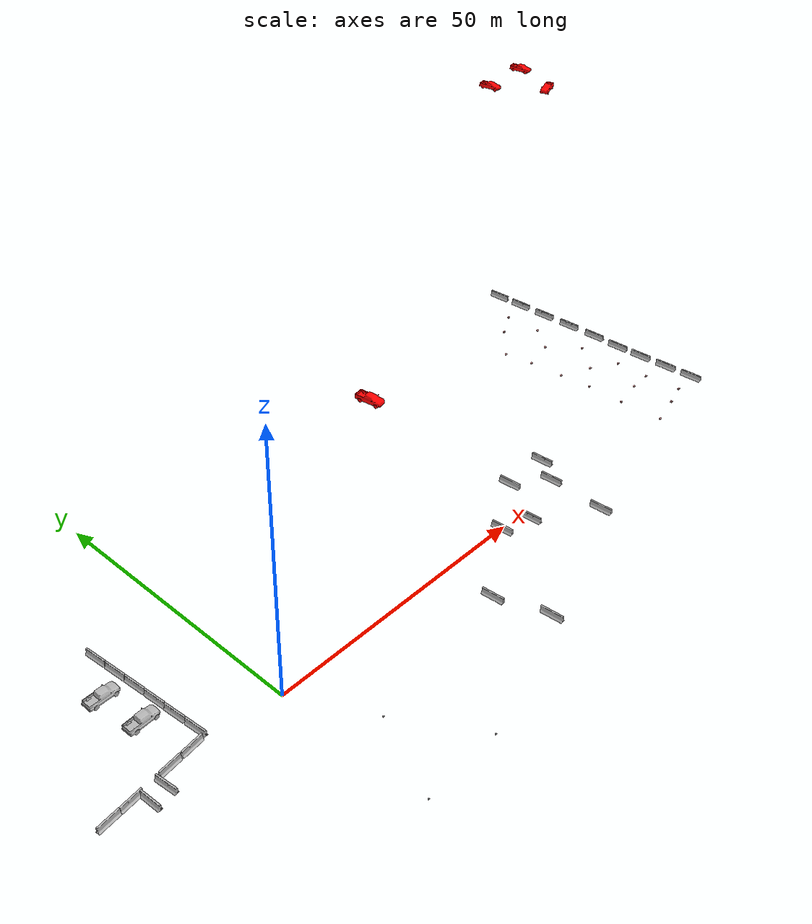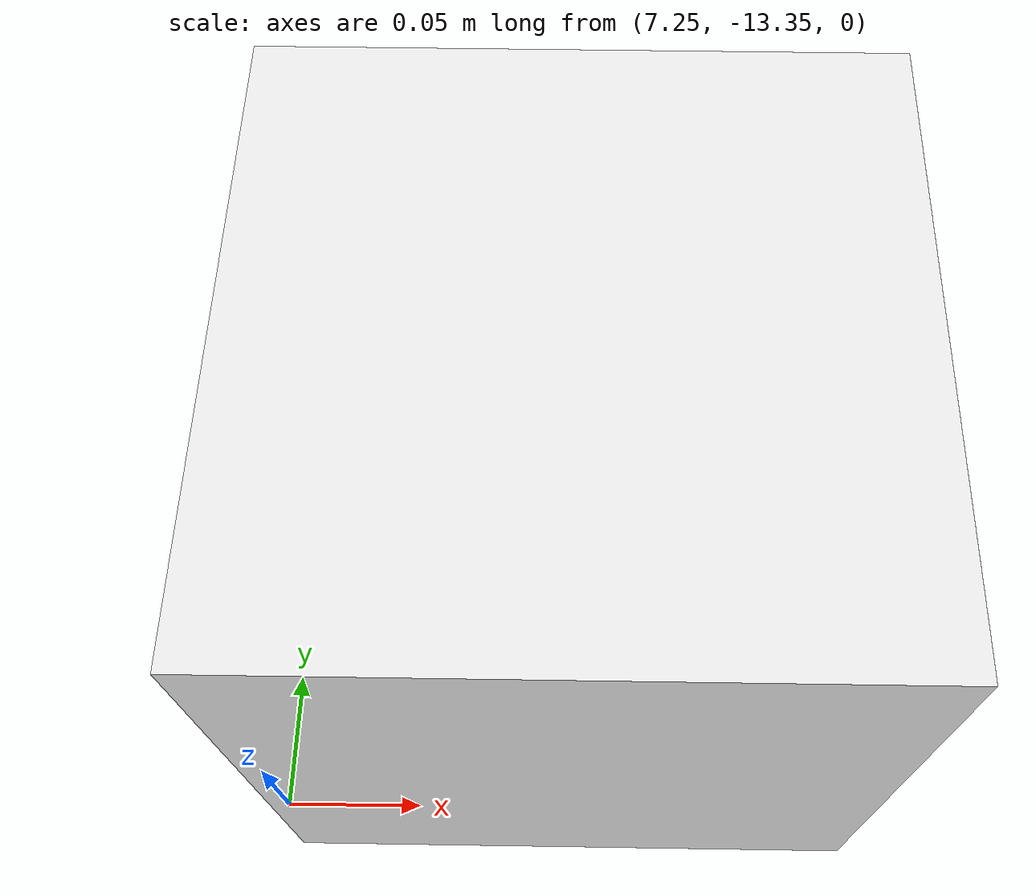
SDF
<sdf version="1.7">
 <world name="default">
  <light name="sun" type="directional">
   <pose>0 0 10 0 -0 0</pose>
   <diffuse>0.8 0.8 0.8 1</diffuse>
   <specular>0.2 0.2 0.2 1</specular>
   <attenuation>
    <range>1000</range>
    <constant>0.9</constant>
    <linear>0.01</linear>
    <quadratic>0.001</quadratic>
   </attenuation>
   <direction>-0.5 0.1 -0.9</direction>
   <spot><inner_angle>0</inner_angle><outer_angle>0</outer_angle><falloff>0</falloff></spot>
  </light>
  <model name="ground_plane">
   <static>1</static>
   <link name="link">
    <collision name="collision">
     <geometry><plane><normal>0 0 1</normal><size>500 500</size></plane></geometry>
     <surface><friction><ode><mu>100</mu><mu2>50</mu2></ode></friction></surface>
    </collision>
    <velocity_decay><linear>0</linear><angular>0</angular></velocity_decay>
   </link>
  </model>
  <physics name="default_physics" default="0" type="ode">
   <max_step_size>0.001</max_step_size>
   <real_time_factor>1</real_time_factor>
   <real_time_update_rate>1000</real_time_update_rate>
  </physics>
  <scene><ambient>0.4 0.4 0.4 1</ambient><background>0.7 0.7 0.7 1</background><shadows>1</shadows></scene>
  <spherical_coordinates>
   <surface_model>EARTH_WGS84</surface_model>
   <latitude_deg>0</latitude_deg>
   <longitude_deg>0</longitude_deg>
   <elevation>0</elevation>
   <heading_deg>0</heading_deg>
  </spherical_coordinates>
  <gravity>0 0 -9.8</gravity>
  <magnetic_field>6e-06 2.3e-05 -4.2e-05</magnetic_field>
  <atmosphere type="adiabatic"/>
  <audio><device>default</device></audio>
  <model name="stone_10_2_5_1cm">
   <link name="link">
    <pose>0 0 0.005 0 -0 0</pose>
    <inertial>
     <mass>0.0628</mass>
     <inertia>
      <ixx>3.79417e-06</ixx>
      <ixy>0</ixy>
      <ixz>0</ixz>
      <iyy>5.28567e-05</iyy>
      <iyz>0</iyz>
      <izz>5.56042e-05</izz>
     </inertia>
    </inertial>
    <collision name="collision">
     <geometry><box><size>0.1 0.025 0.01</size></box></geometry>
     <surface>
      <contact>
       <poissons_ratio>0.15</poissons_ratio>
       <elastic_modulus>8e+10</elastic_modulus>
       <ode><kp>100000</kp><kd>100</kd><max_vel>100</max_vel><min_depth>0.001</min_depth></ode>
      </contact>
      <friction>
       <torsional>
        <coefficient>1</coefficient>
        <use_patch_radius>0</use_patch_radius>
        <surface_radius>0.01</surface_radius>
       </torsional>
      </friction>
     </surface>
    </collision>
    <visual name="visual">
     <geometry><box><size>0.1 0.025 0.01</size></box></geometry>
     <material>
      <script><uri>file://media/materials/scripts/gazebo.material</uri><name>Gazebo/Grey</name></script>
     </material>
    </visual>
   </link>
   <pose>-10.7066 3.01548 -0.001001 0 -0 0</pose>
  </model>
  <model name="jersey_barrier">
   <static>1</static>
   <link name="link">
    <visual name="visual">
     <geometry><mesh><uri>model://jersey barrier/meshes/jersey_barrier.dae</uri></mesh></geometry>
    </visual>
    <collision name="upright">
     <pose>0 0 0.5715 0 -0 0</pose>
     <geometry><box><size>4.06542 0.3063 1.143</size></box></geometry>
    </collision>
    <collision name="base">
     <pose>0 0 0.032258 0 -0 0</pose>
     <geometry><box><size>4.06542 0.8107 0.064516</size></box></geometry>
    </collision>
    <collision name="base2">
     <pose>0 0 0.1 0 -0 0</pose>
     <geometry><box><size>4.06542 0.65 0.1</size></box></geometry>
    </collision>
    <collision name="base3">
     <pose>0 0 0.2 0 -0 0</pose>
     <geometry><box><size>4.06542 0.5 0.1</size></box></geometry>
    </collision>
    <collision name="left-angle">
     <pose>0 -0.224 0.2401 0.9 -0 0</pose>
     <geometry><box><size>4.06542 0.5 0.064516</size></box></geometry>
    </collision>
    <collision name="right-angle">
     <pose>0 0.224 0.2401 -0.9 0 0</pose>
     <geometry><box><size>4.06542 0.5 0.064516</size></box></geometry>
    </collision>
   </link>
   <pose>-14.4169 25.1493 0 0 0 -1.47682</pose>
  </model>
  <model name="jersey_barrier_clone">
   <static>1</static>
   <link name="link">
    <visual name="visual">
     <geometry><mesh><uri>model://jersey barrier/meshes/jersey_barrier.dae</uri></mesh></geometry>
    </visual>
    <collision name="upright">
     <pose>0 0 0.5715 0 -0 0</pose>
     <geometry><box><size>4.06542 0.3063 1.143</size></box></geometry>
    </collision>
    <collision name="base">
     <pose>0 0 0.032258 0 -0 0</pose>
     <geometry><box><size>4.06542 0.8107 0.064516</size></box></geometry>
    </collision>
    <collision name="base2">
     <pose>0 0 0.1 0 -0 0</pose>
     <geometry><box><size>4.06542 0.65 0.1</size></box></geometry>
    </collision>
    <collision name="base3">
     <pose>0 0 0.2 0 -0 0</pose>
     <geometry><box><size>4.06542 0.5 0.1</size></box></geometry>
    </collision>
    <collision name="left-angle">
     <pose>0 -0.224 0.2401 0.9 -0 0</pose>
     <geometry><box><size>4.06542 0.5 0.064516</size></box></geometry>
    </collision>
    <collision name="right-angle">
     <pose>0 0.224 0.2401 -0.9 0 0</pose>
     <geometry><box><size>4.06542 0.5 0.064516</size></box></geometry>
    </collision>
   </link>
   <pose>-14.0333 20.9652 0 0 0 -1.47682</pose>
  </model>
  <model name="jersey_barrier_clone_0">
   <static>1</static>
   <link name="link">
    <visual name="visual">
     <geometry><mesh><uri>model://jersey barrier/meshes/jersey_barrier.dae</uri></mesh></geometry>
    </visual>
    <collision name="upright">
     <pose>0 0 0.5715 0 -0 0</pose>
     <geometry><box><size>4.06542 0.3063 1.143</size></box></geometry>
    </collision>
    <collision name="base">
     <pose>0 0 0.032258 0 -0 0</pose>
     <geometry><box><size>4.06542 0.8107 0.064516</size></box></geometry>
    </collision>
    <collision name="base2">
     <pose>0 0 0.1 0 -0 0</pose>
     <geometry><box><size>4.06542 0.65 0.1</size></box></geometry>
    </collision>
    <collision name="base3">
     <pose>0 0 0.2 0 -0 0</pose>
     <geometry><box><size>4.06542 0.5 0.1</size></box></geometry>
    </collision>
    <collision name="left-angle">
     <pose>0 -0.224 0.2401 0.9 -0 0</pose>
     <geometry><box><size>4.06542 0.5 0.064516</size></box></geometry>
    </collision>
    <collision name="right-angle">
     <pose>0 0.224 0.2401 -0.9 0 0</pose>
     <geometry><box><size>4.06542 0.5 0.064516</size></box></geometry>
    </collision>
   </link>
   <pose>-13.649 16.8026 0 0 0 -1.47682</pose>
  </model>
  <model name="jersey_barrier_clone_1">
   <static>1</static>
   <link name="link">
    <visual name="visual">
     <geometry><mesh><uri>model://jersey barrier/meshes/jersey_barrier.dae</uri></mesh></geometry>
    </visual>
    <collision name="upright">
     <pose>0 0 0.5715 0 -0 0</pose>
     <geometry><box><size>4.06542 0.3063 1.143</size></box></geometry>
    </collision>
    <collision name="base">
     <pose>0 0 0.032258 0 -0 0</pose>
     <geometry><box><size>4.06542 0.8107 0.064516</size></box></geometry>
    </collision>
    <collision name="base2">
     <pose>0 0 0.1 0 -0 0</pose>
     <geometry><box><size>4.06542 0.65 0.1</size></box></geometry>
    </collision>
    <collision name="base3">
     <pose>0 0 0.2 0 -0 0</pose>
     <geometry><box><size>4.06542 0.5 0.1</size></box></geometry>
    </collision>
    <collision name="left-angle">
     <pose>0 -0.224 0.2401 0.9 -0 0</pose>
     <geometry><box><size>4.06542 0.5 0.064516</size></box></geometry>
    </collision>
    <collision name="right-angle">
     <pose>0 0.224 0.2401 -0.9 0 0</pose>
     <geometry><box><size>4.06542 0.5 0.064516</size></box></geometry>
    </collision>
   </link>
   <pose>-12.9437 8.46432 0 0 0 -1.47682</pose>
  </model>
  <model name="jersey_barrier_clone_2">
   <static>1</static>
   <link name="link">
    <visual name="visual">
     <geometry><mesh><uri>model://jersey barrier/meshes/jersey_barrier.dae</uri></mesh></geometry>
    </visual>
    <collision name="upright">
     <pose>0 0 0.5715 0 -0 0</pose>
     <geometry><box><size>4.06542 0.3063 1.143</size></box></geometry>
    </collision>
    <collision name="base">
     <pose>0 0 0.032258 0 -0 0</pose>
     <geometry><box><size>4.06542 0.8107 0.064516</size></box></geometry>
    </collision>
    <collision name="base2">
     <pose>0 0 0.1 0 -0 0</pose>
     <geometry><box><size>4.06542 0.65 0.1</size></box></geometry>
    </collision>
    <collision name="base3">
     <pose>0 0 0.2 0 -0 0</pose>
     <geometry><box><size>4.06542 0.5 0.1</size></box></geometry>
    </collision>
    <collision name="left-angle">
     <pose>0 -0.224 0.2401 0.9 -0 0</pose>
     <geometry><box><size>4.06542 0.5 0.064516</size></box></geometry>
    </collision>
    <collision name="right-angle">
     <pose>0 0.224 0.2401 -0.9 0 0</pose>
     <geometry><box><size>4.06542 0.5 0.064516</size></box></geometry>
    </collision>
   </link>
   <pose>-15.0314 2.21816 0 0 -0 0.11035</pose>
  </model>
  <model name="jersey_barrier_clone_2_clone">
   <static>1</static>
   <link name="link">
    <visual name="visual">
     <geometry><mesh><uri>model://jersey barrier/meshes/jersey_barrier.dae</uri></mesh></geometry>
    </visual>
    <collision name="upright">
     <pose>0 0 0.5715 0 -0 0</pose>
     <geometry><box><size>4.06542 0.3063 1.143</size></box></geometry>
    </collision>
    <collision name="base">
     <pose>0 0 0.032258 0 -0 0</pose>
     <geometry><box><size>4.06542 0.8107 0.064516</size></box></geometry>
    </collision>
    <collision name="base2">
     <pose>0 0 0.1 0 -0 0</pose>
     <geometry><box><size>4.06542 0.65 0.1</size></box></geometry>
    </collision>
    <collision name="base3">
     <pose>0 0 0.2 0 -0 0</pose>
     <geometry><box><size>4.06542 0.5 0.1</size></box></geometry>
    </collision>
    <collision name="left-angle">
     <pose>0 -0.224 0.2401 0.9 -0 0</pose>
     <geometry><box><size>4.06542 0.5 0.064516</size></box></geometry>
    </collision>
    <collision name="right-angle">
     <pose>0 0.224 0.2401 -0.9 0 0</pose>
     <geometry><box><size>4.06542 0.5 0.064516</size></box></geometry>
    </collision>
   </link>
   <pose>-19.2855 1.77483 0 0 -0 0.106437</pose>
  </model>
  <model name="jersey_barrier_clone_0_clone">
   <static>1</static>
   <link name="link">
    <visual name="visual">
     <geometry><mesh><uri>model://jersey barrier/meshes/jersey_barrier.dae</uri></mesh></geometry>
    </visual>
    <collision name="upright">
     <pose>0 0 0.5715 0 -0 0</pose>
     <geometry><box><size>4.06542 0.3063 1.143</size></box></geometry>
    </collision>
    <collision name="base">
     <pose>0 0 0.032258 0 -0 0</pose>
     <geometry><box><size>4.06542 0.8107 0.064516</size></box></geometry>
    </collision>
    <collision name="base2">
     <pose>0 0 0.1 0 -0 0</pose>
     <geometry><box><size>4.06542 0.65 0.1</size></box></geometry>
    </collision>
    <collision name="base3">
     <pose>0 0 0.2 0 -0 0</pose>
     <geometry><box><size>4.06542 0.5 0.1</size></box></geometry>
    </collision>
    <collision name="left-angle">
     <pose>0 -0.224 0.2401 0.9 -0 0</pose>
     <geometry><box><size>4.06542 0.5 0.064516</size></box></geometry>
    </collision>
    <collision name="right-angle">
     <pose>0 0.224 0.2401 -0.9 0 0</pose>
     <geometry><box><size>4.06542 0.5 0.064516</size></box></geometry>
    </collision>
   </link>
   <pose>39.4339 -18.3979 0 0 0 -1.47682</pose>
  </model>
  <model name="jersey_barrier_clone_0_clone_0">
   <static>1</static>
   <link name="link">
    <visual name="visual">
     <geometry><mesh><uri>model://jersey barrier/meshes/jersey_barrier.dae</uri></mesh></geometry>
    </visual>
    <collision name="upright">
     <pose>0 0 0.5715 0 -0 0</pose>
     <geometry><box><size>4.06542 0.3063 1.143</size></box></geometry>
    </collision>
    <collision name="base">
     <pose>0 0 0.032258 0 -0 0</pose>
     <geometry><box><size>4.06542 0.8107 0.064516</size></box></geometry>
    </collision>
    <collision name="base2">
     <pose>0 0 0.1 0 -0 0</pose>
     <geometry><box><size>4.06542 0.65 0.1</size></box></geometry>
    </collision>
    <collision name="base3">
     <pose>0 0 0.2 0 -0 0</pose>
     <geometry><box><size>4.06542 0.5 0.1</size></box></geometry>
    </collision>
    <collision name="left-angle">
     <pose>0 -0.224 0.2401 0.9 -0 0</pose>
     <geometry><box><size>4.06542 0.5 0.064516</size></box></geometry>
    </collision>
    <collision name="right-angle">
     <pose>0 0.224 0.2401 -0.9 0 0</pose>
     <geometry><box><size>4.06542 0.5 0.064516</size></box></geometry>
    </collision>
   </link>
   <pose>36.133 -9.29437 0 0 0 -1.47682</pose>
  </model>
  <model name="jersey_barrier_clone_0_clone_1">
   <static>1</static>
   <link name="link">
    <visual name="visual">
     <geometry><mesh><uri>model://jersey barrier/meshes/jersey_barrier.dae</uri></mesh></geometry>
    </visual>
    <collision name="upright">
     <pose>0 0 0.5715 0 -0 0</pose>
     <geometry><box><size>4.06542 0.3063 1.143</size></box></geometry>
    </collision>
    <collision name="base">
     <pose>0 0 0.032258 0 -0 0</pose>
     <geometry><box><size>4.06542 0.8107 0.064516</size></box></geometry>
    </collision>
    <collision name="base2">
     <pose>0 0 0.1 0 -0 0</pose>
     <geometry><box><size>4.06542 0.65 0.1</size></box></geometry>
    </collision>
    <collision name="base3">
     <pose>0 0 0.2 0 -0 0</pose>
     <geometry><box><size>4.06542 0.5 0.1</size></box></geometry>
    </collision>
    <collision name="left-angle">
     <pose>0 -0.224 0.2401 0.9 -0 0</pose>
     <geometry><box><size>4.06542 0.5 0.064516</size></box></geometry>
    </collision>
    <collision name="right-angle">
     <pose>0 0.224 0.2401 -0.9 0 0</pose>
     <geometry><box><size>4.06542 0.5 0.064516</size></box></geometry>
    </collision>
   </link>
   <pose>49.1509 -0.2917 0 0 0 -1.47682</pose>
  </model>
  <model name="jersey_barrier_clone_0_clone_2">
   <static>1</static>
   <link name="link">
    <visual name="visual">
     <geometry><mesh><uri>model://jersey barrier/meshes/jersey_barrier.dae</uri></mesh></geometry>
    </visual>
    <collision name="upright">
     <pose>0 0 0.5715 0 -0 0</pose>
     <geometry><box><size>4.06542 0.3063 1.143</size></box></geometry>
    </collision>
    <collision name="base">
     <pose>0 0 0.032258 0 -0 0</pose>
     <geometry><box><size>4.06542 0.8107 0.064516</size></box></geometry>
    </collision>
    <collision name="base2">
     <pose>0 0 0.1 0 -0 0</pose>
     <geometry><box><size>4.06542 0.65 0.1</size></box></geometry>
    </collision>
    <collision name="base3">
     <pose>0 0 0.2 0 -0 0</pose>
     <geometry><box><size>4.06542 0.5 0.1</size></box></geometry>
    </collision>
    <collision name="left-angle">
     <pose>0 -0.224 0.2401 0.9 -0 0</pose>
     <geometry><box><size>4.06542 0.5 0.064516</size></box></geometry>
    </collision>
    <collision name="right-angle">
     <pose>0 0.224 0.2401 -0.9 0 0</pose>
     <geometry><box><size>4.06542 0.5 0.064516</size></box></geometry>
    </collision>
   </link>
   <pose>54.5121 -1.92489 0 0 0 -1.47682</pose>
  </model>
  <model name="jersey_barrier_clone_0_clone_3">
   <static>1</static>
   <link name="link">
    <visual name="visual">
     <geometry><mesh><uri>model://jersey barrier/meshes/jersey_barrier.dae</uri></mesh></geometry>
    </visual>
    <collision name="upright">
     <pose>0 0 0.5715 0 -0 0</pose>
     <geometry><box><size>4.06542 0.3063 1.143</size></box></geometry>
    </collision>
    <collision name="base">
     <pose>0 0 0.032258 0 -0 0</pose>
     <geometry><box><size>4.06542 0.8107 0.064516</size></box></geometry>
    </collision>
    <collision name="base2">
     <pose>0 0 0.1 0 -0 0</pose>
     <geometry><box><size>4.06542 0.65 0.1</size></box></geometry>
    </collision>
    <collision name="base3">
     <pose>0 0 0.2 0 -0 0</pose>
     <geometry><box><size>4.06542 0.5 0.1</size></box></geometry>
    </collision>
    <collision name="left-angle">
     <pose>0 -0.224 0.2401 0.9 -0 0</pose>
     <geometry><box><size>4.06542 0.5 0.064516</size></box></geometry>
    </collision>
    <collision name="right-angle">
     <pose>0 0.224 0.2401 -0.9 0 0</pose>
     <geometry><box><size>4.06542 0.5 0.064516</size></box></geometry>
    </collision>
   </link>
   <pose>64.4516 -9.04992 0 0 0 -1.47682</pose>
  </model>
  <model name="jersey_barrier_clone_0_clone_4">
   <static>1</static>
   <link name="link">
    <visual name="visual">
     <geometry><mesh><uri>model://jersey barrier/meshes/jersey_barrier.dae</uri></mesh></geometry>
    </visual>
    <collision name="upright">
     <pose>0 0 0.5715 0 -0 0</pose>
     <geometry><box><size>4.06542 0.3063 1.143</size></box></geometry>
    </collision>
    <collision name="base">
     <pose>0 0 0.032258 0 -0 0</pose>
     <geometry><box><size>4.06542 0.8107 0.064516</size></box></geometry>
    </collision>
    <collision name="base2">
     <pose>0 0 0.1 0 -0 0</pose>
     <geometry><box><size>4.06542 0.65 0.1</size></box></geometry>
    </collision>
    <collision name="base3">
     <pose>0 0 0.2 0 -0 0</pose>
     <geometry><box><size>4.06542 0.5 0.1</size></box></geometry>
    </collision>
    <collision name="left-angle">
     <pose>0 -0.224 0.2401 0.9 -0 0</pose>
     <geometry><box><size>4.06542 0.5 0.064516</size></box></geometry>
    </collision>
    <collision name="right-angle">
     <pose>0 0.224 0.2401 -0.9 0 0</pose>
     <geometry><box><size>4.06542 0.5 0.064516</size></box></geometry>
    </collision>
   </link>
   <pose>64.5642 1.62227 0 0 0 -1.47682</pose>
  </model>
  <model name="jersey_barrier_clone_0_clone_5">
   <static>1</static>
   <link name="link">
    <visual name="visual">
     <geometry><mesh><uri>model://jersey barrier/meshes/jersey_barrier.dae</uri></mesh></geometry>
    </visual>
    <collision name="upright">
     <pose>0 0 0.5715 0 -0 0</pose>
     <geometry><box><size>4.06542 0.3063 1.143</size></box></geometry>
    </collision>
    <collision name="base">
     <pose>0 0 0.032258 0 -0 0</pose>
     <geometry><box><size>4.06542 0.8107 0.064516</size></box></geometry>
    </collision>
    <collision name="base2">
     <pose>0 0 0.1 0 -0 0</pose>
     <geometry><box><size>4.06542 0.65 0.1</size></box></geometry>
    </collision>
    <collision name="base3">
     <pose>0 0 0.2 0 -0 0</pose>
     <geometry><box><size>4.06542 0.5 0.1</size></box></geometry>
    </collision>
    <collision name="left-angle">
     <pose>0 -0.224 0.2401 0.9 -0 0</pose>
     <geometry><box><size>4.06542 0.5 0.064516</size></box></geometry>
    </collision>
    <collision name="right-angle">
     <pose>0 0.224 0.2401 -0.9 0 0</pose>
     <geometry><box><size>4.06542 0.5 0.064516</size></box></geometry>
    </collision>
   </link>
   <pose>67.4973 6 0 0 0 -1.47682</pose>
  </model>
  <model name="jersey_barrier_clone_0_clone_6">
   <static>1</static>
   <link name="link">
    <visual name="visual">
     <geometry><mesh><uri>model://jersey barrier/meshes/jersey_barrier.dae</uri></mesh></geometry>
    </visual>
    <collision name="upright">
     <pose>0 0 0.5715 0 -0 0</pose>
     <geometry><box><size>4.06542 0.3063 1.143</size></box></geometry>
    </collision>
    <collision name="base">
     <pose>0 0 0.032258 0 -0 0</pose>
     <geometry><box><size>4.06542 0.8107 0.064516</size></box></geometry>
    </collision>
    <collision name="base2">
     <pose>0 0 0.1 0 -0 0</pose>
     <geometry><box><size>4.06542 0.65 0.1</size></box></geometry>
    </collision>
    <collision name="base3">
     <pose>0 0 0.2 0 -0 0</pose>
     <geometry><box><size>4.06542 0.5 0.1</size></box></geometry>
    </collision>
    <collision name="left-angle">
     <pose>0 -0.224 0.2401 0.9 -0 0</pose>
     <geometry><box><size>4.06542 0.5 0.064516</size></box></geometry>
    </collision>
    <collision name="right-angle">
     <pose>0 0.224 0.2401 -0.9 0 0</pose>
     <geometry><box><size>4.06542 0.5 0.064516</size></box></geometry>
    </collision>
   </link>
   <pose>58.825 6.11774 0 0 0 -1.47682</pose>
  </model>
  <model name="mine">
   <link name="link">
    <inertial>
     <mass>1</mass>
     <inertia>
      <ixx>0.166667</ixx>
      <ixy>0</ixy>
      <ixz>0</ixz>
      <iyy>0.166667</iyy>
      <iyz>0</iyz>
      <izz>0.166667</izz>
     </inertia>
    </inertial>
    <visual name="visual">
     <geometry><box><size>0.35 0.35 0.2</size></box></geometry>
     <material>
      <script><name>Gazebo/Grey</name><uri>file://media/materials/scripts/gazebo.material</uri></script>
      <shader type="pixel"><normal_map>__default__</normal_map></shader>
      <diffuse>1 0.7 0.7 1</diffuse>
      <ambient>0.3 0.3 0.3 1</ambient>
      <specular>0.01 0.01 0.01 1</specular>
      <emissive>1 0.7 0 1</emissive>
      <lighting>1</lighting>
     </material>
    </visual>
    <collision name="collision">
     <geometry><box><size>0.35 0.35 0.2</size></box></geometry>
     <surface>
      <friction>
       <ode><mu>1</mu><mu2>1</mu2><fdir1>0 0 0</fdir1><slip1>0</slip1><slip2>0</slip2></ode>
       <torsional>
        <coefficient>1</coefficient>
        <patch_radius>0</patch_radius>
        <surface_radius>0</surface_radius>
        <use_patch_radius>1</use_patch_radius>
        <ode><slip>0</slip></ode>
       </torsional>
      </friction>
      <bounce><restitution_coefficient>0</restitution_coefficient><threshold>1e+06</threshold></bounce>
      <contact>
       <collide_without_contact>0</collide_without_contact>
       <collide_without_contact_bitmask>1</collide_without_contact_bitmask>
       <collide_bitmask>1</collide_bitmask>
       <ode>
        <soft_cfm>0</soft_cfm>
        <soft_erp>0.2</soft_erp>
        <kp>1e+13</kp>
        <kd>1</kd>
        <max_vel>0.01</max_vel>
        <min_depth>0</min_depth>
       </ode>
       <bullet>
        <split_impulse>1</split_impulse>
        <split_impulse_penetration_threshold>-0.01</split_impulse_penetration_threshold>
        <soft_cfm>0</soft_cfm>
        <soft_erp>0.2</soft_erp>
        <kp>1e+13</kp>
        <kd>1</kd>
       </bullet>
      </contact>
     </surface>
    </collision>
   </link>
   <static>0</static>
   <pose>98.4312 39.3089 0.099997 7e-06 -7e-06 -1.28503</pose>
  </model>
  <model name="mine_clone">
   <link name="link">
    <inertial>
     <mass>1</mass>
     <inertia>
      <ixx>0.166667</ixx>
      <ixy>0</ixy>
      <ixz>0</ixz>
      <iyy>0.166667</iyy>
      <iyz>0</iyz>
      <izz>0.166667</izz>
     </inertia>
    </inertial>
    <visual name="visual">
     <geometry><box><size>0.35 0.35 0.2</size></box></geometry>
     <material>
      <script><name>Gazebo/Grey</name><uri>file://media/materials/scripts/gazebo.material</uri></script>
      <shader type="pixel"><normal_map>__default__</normal_map></shader>
      <diffuse>1 0.7 0.7 1</diffuse>
      <ambient>0.3 0.3 0.3 1</ambient>
      <specular>0.01 0.01 0.01 1</specular>
      <emissive>1 0.7 0 1</emissive>
      <lighting>1</lighting>
     </material>
    </visual>
    <collision name="collision">
     <geometry><box><size>0.35 0.35 0.2</size></box></geometry>
     <surface>
      <friction>
       <ode><mu>1</mu><mu2>1</mu2><fdir1>0 0 0</fdir1><slip1>0</slip1><slip2>0</slip2></ode>
       <torsional>
        <coefficient>1</coefficient>
        <patch_radius>0</patch_radius>
        <surface_radius>0</surface_radius>
        <use_patch_radius>1</use_patch_radius>
        <ode><slip>0</slip></ode>
       </torsional>
      </friction>
      <bounce><restitution_coefficient>0</restitution_coefficient><threshold>1e+06</threshold></bounce>
      <contact>
       <collide_without_contact>0</collide_without_contact>
       <collide_without_contact_bitmask>1</collide_without_contact_bitmask>
       <collide_bitmask>1</collide_bitmask>
       <ode>
        <soft_cfm>0</soft_cfm>
        <soft_erp>0.2</soft_erp>
        <kp>1e+13</kp>
        <kd>1</kd>
        <max_vel>0.01</max_vel>
        <min_depth>0</min_depth>
       </ode>
       <bullet>
        <split_impulse>1</split_impulse>
        <split_impulse_penetration_threshold>-0.01</split_impulse_penetration_threshold>
        <soft_cfm>0</soft_cfm>
        <soft_erp>0.2</soft_erp>
        <kp>1e+13</kp>
        <kd>1</kd>
       </bullet>
      </contact>
     </surface>
    </collision>
   </link>
   <static>0</static>
   <pose>93.7959 36.654 0.099997 7e-06 -7e-06 -1.28503</pose>
  </model>
  <model name="mine_clone_0">
   <link name="link">
    <inertial>
     <mass>1</mass>
     <inertia>
      <ixx>0.166667</ixx>
      <ixy>0</ixy>
      <ixz>0</ixz>
      <iyy>0.166667</iyy>
      <iyz>0</iyz>
      <izz>0.166667</izz>
     </inertia>
    </inertial>
    <visual name="visual">
     <geometry><box><size>0.35 0.35 0.2</size></box></geometry>
     <material>
      <script><name>Gazebo/Grey</name><uri>file://media/materials/scripts/gazebo.material</uri></script>
      <shader type="pixel"><normal_map>__default__</normal_map></shader>
      <diffuse>1 0.7 0.7 1</diffuse>
      <ambient>0.3 0.3 0.3 1</ambient>
      <specular>0.01 0.01 0.01 1</specular>
      <emissive>1 0.7 0 1</emissive>
      <lighting>1</lighting>
     </material>
    </visual>
    <collision name="collision">
     <geometry><box><size>0.35 0.35 0.2</size></box></geometry>
     <surface>
      <friction>
       <ode><mu>1</mu><mu2>1</mu2><fdir1>0 0 0</fdir1><slip1>0</slip1><slip2>0</slip2></ode>
       <torsional>
        <coefficient>1</coefficient>
        <patch_radius>0</patch_radius>
        <surface_radius>0</surface_radius>
        <use_patch_radius>1</use_patch_radius>
        <ode><slip>0</slip></ode>
       </torsional>
      </friction>
      <bounce><restitution_coefficient>0</restitution_coefficient><threshold>1e+06</threshold></bounce>
      <contact>
       <collide_without_contact>0</collide_without_contact>
       <collide_without_contact_bitmask>1</collide_without_contact_bitmask>
       <collide_bitmask>1</collide_bitmask>
       <ode>
        <soft_cfm>0</soft_cfm>
        <soft_erp>0.2</soft_erp>
        <kp>1e+13</kp>
        <kd>1</kd>
        <max_vel>0.01</max_vel>
        <min_depth>0</min_depth>
       </ode>
       <bullet>
        <split_impulse>1</split_impulse>
        <split_impulse_penetration_threshold>-0.01</split_impulse_penetration_threshold>
        <soft_cfm>0</soft_cfm>
        <soft_erp>0.2</soft_erp>
        <kp>1e+13</kp>
        <kd>1</kd>
       </bullet>
      </contact>
     </surface>
    </collision>
   </link>
   <static>0</static>
   <pose>88.1406 31.4287 0.099997 7e-06 -7e-06 -1.28503</pose>
  </model>
  <model name="mine_clone_1">
   <link name="link">
    <inertial>
     <mass>1</mass>
     <inertia>
      <ixx>0.166667</ixx>
      <ixy>0</ixy>
      <ixz>0</ixz>
      <iyy>0.166667</iyy>
      <iyz>0</iyz>
      <izz>0.166667</izz>
     </inertia>
    </inertial>
    <visual name="visual">
     <geometry><box><size>0.35 0.35 0.2</size></box></geometry>
     <material>
      <script><name>Gazebo/Grey</name><uri>file://media/materials/scripts/gazebo.material</uri></script>
      <shader type="pixel"><normal_map>__default__</normal_map></shader>
      <diffuse>1 0.7 0.7 1</diffuse>
      <ambient>0.3 0.3 0.3 1</ambient>
      <specular>0.01 0.01 0.01 1</specular>
      <emissive>1 0.7 0 1</emissive>
      <lighting>1</lighting>
     </material>
    </visual>
    <collision name="collision">
     <geometry><box><size>0.35 0.35 0.2</size></box></geometry>
     <surface>
      <friction>
       <ode><mu>1</mu><mu2>1</mu2><fdir1>0 0 0</fdir1><slip1>0</slip1><slip2>0</slip2></ode>
       <torsional>
        <coefficient>1</coefficient>
        <patch_radius>0</patch_radius>
        <surface_radius>0</surface_radius>
        <use_patch_radius>1</use_patch_radius>
        <ode><slip>0</slip></ode>
       </torsional>
      </friction>
      <bounce><restitution_coefficient>0</restitution_coefficient><threshold>1e+06</threshold></bounce>
      <contact>
       <collide_without_contact>0</collide_without_contact>
       <collide_without_contact_bitmask>1</collide_without_contact_bitmask>
       <collide_bitmask>1</collide_bitmask>
       <ode>
        <soft_cfm>0</soft_cfm>
        <soft_erp>0.2</soft_erp>
        <kp>1e+13</kp>
        <kd>1</kd>
        <max_vel>0.01</max_vel>
        <min_depth>0</min_depth>
       </ode>
       <bullet>
        <split_impulse>1</split_impulse>
        <split_impulse_penetration_threshold>-0.01</split_impulse_penetration_threshold>
        <soft_cfm>0</soft_cfm>
        <soft_erp>0.2</soft_erp>
        <kp>1e+13</kp>
        <kd>1</kd>
       </bullet>
      </contact>
     </surface>
    </collision>
   </link>
   <static>0</static>
   <pose>98.8148 32.1679 0.099997 7e-06 -7e-06 -1.28503</pose>
  </model>
  <model name="mine_clone_2">
   <link name="link">
    <inertial>
     <mass>1</mass>
     <inertia>
      <ixx>0.166667</ixx>
      <ixy>0</ixy>
      <ixz>0</ixz>
      <iyy>0.166667</iyy>
      <iyz>0</iyz>
      <izz>0.166667</izz>
     </inertia>
    </inertial>
    <visual name="visual">
     <geometry><box><size>0.35 0.35 0.2</size></box></geometry>
     <material>
      <script><name>Gazebo/Grey</name><uri>file://media/materials/scripts/gazebo.material</uri></script>
      <shader type="pixel"><normal_map>__default__</normal_map></shader>
      <diffuse>1 0.7 0.7 1</diffuse>
      <ambient>0.3 0.3 0.3 1</ambient>
      <specular>0.01 0.01 0.01 1</specular>
      <emissive>1 0.7 0 1</emissive>
      <lighting>1</lighting>
     </material>
    </visual>
    <collision name="collision">
     <geometry><box><size>0.35 0.35 0.2</size></box></geometry>
     <surface>
      <friction>
       <ode><mu>1</mu><mu2>1</mu2><fdir1>0 0 0</fdir1><slip1>0</slip1><slip2>0</slip2></ode>
       <torsional>
        <coefficient>1</coefficient>
        <patch_radius>0</patch_radius>
        <surface_radius>0</surface_radius>
        <use_patch_radius>1</use_patch_radius>
        <ode><slip>0</slip></ode>
       </torsional>
      </friction>
      <bounce><restitution_coefficient>0</restitution_coefficient><threshold>1e+06</threshold></bounce>
      <contact>
       <collide_without_contact>0</collide_without_contact>
       <collide_without_contact_bitmask>1</collide_without_contact_bitmask>
       <collide_bitmask>1</collide_bitmask>
       <ode>
        <soft_cfm>0</soft_cfm>
        <soft_erp>0.2</soft_erp>
        <kp>1e+13</kp>
        <kd>1</kd>
        <max_vel>0.01</max_vel>
        <min_depth>0</min_depth>
       </ode>
       <bullet>
        <split_impulse>1</split_impulse>
        <split_impulse_penetration_threshold>-0.01</split_impulse_penetration_threshold>
        <soft_cfm>0</soft_cfm>
        <soft_erp>0.2</soft_erp>
        <kp>1e+13</kp>
        <kd>1</kd>
       </bullet>
      </contact>
     </surface>
    </collision>
   </link>
   <static>0</static>
   <pose>95.3052 27.4382 0.099997 7e-06 -7e-06 -1.28503</pose>
  </model>
  <model name="mine_clone_3">
   <link name="link">
    <inertial>
     <mass>1</mass>
     <inertia>
      <ixx>0.166667</ixx>
      <ixy>0</ixy>
      <ixz>0</ixz>
      <iyy>0.166667</iyy>
      <iyz>0</iyz>
      <izz>0.166667</izz>
     </inertia>
    </inertial>
    <visual name="visual">
     <geometry><box><size>0.35 0.35 0.2</size></box></geometry>
     <material>
      <script><name>Gazebo/Grey</name><uri>file://media/materials/scripts/gazebo.material</uri></script>
      <shader type="pixel"><normal_map>__default__</normal_map></shader>
      <diffuse>1 0.7 0.7 1</diffuse>
      <ambient>0.3 0.3 0.3 1</ambient>
      <specular>0.01 0.01 0.01 1</specular>
      <emissive>1 0.7 0 1</emissive>
      <lighting>1</lighting>
     </material>
    </visual>
    <collision name="collision">
     <geometry><box><size>0.35 0.35 0.2</size></box></geometry>
     <surface>
      <friction>
       <ode><mu>1</mu><mu2>1</mu2><fdir1>0 0 0</fdir1><slip1>0</slip1><slip2>0</slip2></ode>
       <torsional>
        <coefficient>1</coefficient>
        <patch_radius>0</patch_radius>
        <surface_radius>0</surface_radius>
        <use_patch_radius>1</use_patch_radius>
        <ode><slip>0</slip></ode>
       </torsional>
      </friction>
      <bounce><restitution_coefficient>0</restitution_coefficient><threshold>1e+06</threshold></bounce>
      <contact>
       <collide_without_contact>0</collide_without_contact>
       <collide_without_contact_bitmask>1</collide_without_contact_bitmask>
       <collide_bitmask>1</collide_bitmask>
       <ode>
        <soft_cfm>0</soft_cfm>
        <soft_erp>0.2</soft_erp>
        <kp>1e+13</kp>
        <kd>1</kd>
        <max_vel>0.01</max_vel>
        <min_depth>0</min_depth>
       </ode>
       <bullet>
        <split_impulse>1</split_impulse>
        <split_impulse_penetration_threshold>-0.01</split_impulse_penetration_threshold>
        <soft_cfm>0</soft_cfm>
        <soft_erp>0.2</soft_erp>
        <kp>1e+13</kp>
        <kd>1</kd>
       </bullet>
      </contact>
     </surface>
    </collision>
   </link>
   <static>0</static>
   <pose>89.2511 25.9904 0.099997 7e-06 -7e-06 -1.28503</pose>
  </model>
  <model name="mine_clone_4">
   <link name="link">
    <inertial>
     <mass>1</mass>
     <inertia>
      <ixx>0.166667</ixx>
      <ixy>0</ixy>
      <ixz>0</ixz>
      <iyy>0.166667</iyy>
      <iyz>0</iyz>
      <izz>0.166667</izz>
     </inertia>
    </inertial>
    <visual name="visual">
     <geometry><box><size>0.35 0.35 0.2</size></box></geometry>
     <material>
      <script><name>Gazebo/Grey</name><uri>file://media/materials/scripts/gazebo.material</uri></script>
      <shader type="pixel"><normal_map>__default__</normal_map></shader>
      <diffuse>1 0.7 0.7 1</diffuse>
      <ambient>0.3 0.3 0.3 1</ambient>
      <specular>0.01 0.01 0.01 1</specular>
      <emissive>1 0.7 0 1</emissive>
      <lighting>1</lighting>
     </material>
    </visual>
    <collision name="collision">
     <geometry><box><size>0.35 0.35 0.2</size></box></geometry>
     <surface>
      <friction>
       <ode><mu>1</mu><mu2>1</mu2><fdir1>0 0 0</fdir1><slip1>0</slip1><slip2>0</slip2></ode>
       <torsional>
        <coefficient>1</coefficient>
        <patch_radius>0</patch_radius>
        <surface_radius>0</surface_radius>
        <use_patch_radius>1</use_patch_radius>
        <ode><slip>0</slip></ode>
       </torsional>
      </friction>
      <bounce><restitution_coefficient>0</restitution_coefficient><threshold>1e+06</threshold></bounce>
      <contact>
       <collide_without_contact>0</collide_without_contact>
       <collide_without_contact_bitmask>1</collide_without_contact_bitmask>
       <collide_bitmask>1</collide_bitmask>
       <ode>
        <soft_cfm>0</soft_cfm>
        <soft_erp>0.2</soft_erp>
        <kp>1e+13</kp>
        <kd>1</kd>
        <max_vel>0.01</max_vel>
        <min_depth>0</min_depth>
       </ode>
       <bullet>
        <split_impulse>1</split_impulse>
        <split_impulse_penetration_threshold>-0.01</split_impulse_penetration_threshold>
        <soft_cfm>0</soft_cfm>
        <soft_erp>0.2</soft_erp>
        <kp>1e+13</kp>
        <kd>1</kd>
       </bullet>
      </contact>
     </surface>
    </collision>
   </link>
   <static>0</static>
   <pose>90.0743 19.3901 0.099997 7e-06 -7e-06 -1.28503</pose>
  </model>
  <model name="mine_clone_5">
   <link name="link">
    <inertial>
     <mass>1</mass>
     <inertia>
      <ixx>0.166667</ixx>
      <ixy>0</ixy>
      <ixz>0</ixz>
      <iyy>0.166667</iyy>
      <iyz>0</iyz>
      <izz>0.166667</izz>
     </inertia>
    </inertial>
    <visual name="visual">
     <geometry><box><size>0.35 0.35 0.2</size></box></geometry>
     <material>
      <script><name>Gazebo/Grey</name><uri>file://media/materials/scripts/gazebo.material</uri></script>
      <shader type="pixel"><normal_map>__default__</normal_map></shader>
      <diffuse>1 0.7 0.7 1</diffuse>
      <ambient>0.3 0.3 0.3 1</ambient>
      <specular>0.01 0.01 0.01 1</specular>
      <emissive>1 0.7 0 1</emissive>
      <lighting>1</lighting>
     </material>
    </visual>
    <collision name="collision">
     <geometry><box><size>0.35 0.35 0.2</size></box></geometry>
     <surface>
      <friction>
       <ode><mu>1</mu><mu2>1</mu2><fdir1>0 0 0</fdir1><slip1>0</slip1><slip2>0</slip2></ode>
       <torsional>
        <coefficient>1</coefficient>
        <patch_radius>0</patch_radius>
        <surface_radius>0</surface_radius>
        <use_patch_radius>1</use_patch_radius>
        <ode><slip>0</slip></ode>
       </torsional>
      </friction>
      <bounce><restitution_coefficient>0</restitution_coefficient><threshold>1e+06</threshold></bounce>
      <contact>
       <collide_without_contact>0</collide_without_contact>
       <collide_without_contact_bitmask>1</collide_without_contact_bitmask>
       <collide_bitmask>1</collide_bitmask>
       <ode>
        <soft_cfm>0</soft_cfm>
        <soft_erp>0.2</soft_erp>
        <kp>1e+13</kp>
        <kd>1</kd>
        <max_vel>0.01</max_vel>
        <min_depth>0</min_depth>
       </ode>
       <bullet>
        <split_impulse>1</split_impulse>
        <split_impulse_penetration_threshold>-0.01</split_impulse_penetration_threshold>
        <soft_cfm>0</soft_cfm>
        <soft_erp>0.2</soft_erp>
        <kp>1e+13</kp>
        <kd>1</kd>
       </bullet>
      </contact>
     </surface>
    </collision>
   </link>
   <static>0</static>
   <pose>90.9245 13.3564 0.099997 7e-06 -7e-06 -1.28503</pose>
  </model>
  <model name="mine_clone_6">
   <link name="link">
    <inertial>
     <mass>1</mass>
     <inertia>
      <ixx>0.166667</ixx>
      <ixy>0</ixy>
      <ixz>0</ixz>
      <iyy>0.166667</iyy>
      <iyz>0</iyz>
      <izz>0.166667</izz>
     </inertia>
    </inertial>
    <visual name="visual">
     <geometry><box><size>0.35 0.35 0.2</size></box></geometry>
     <material>
      <script><name>Gazebo/Grey</name><uri>file://media/materials/scripts/gazebo.material</uri></script>
      <shader type="pixel"><normal_map>__default__</normal_map></shader>
      <diffuse>1 0.7 0.7 1</diffuse>
      <ambient>0.3 0.3 0.3 1</ambient>
      <specular>0.01 0.01 0.01 1</specular>
      <emissive>1 0.7 0 1</emissive>
      <lighting>1</lighting>
     </material>
    </visual>
    <collision name="collision">
     <geometry><box><size>0.35 0.35 0.2</size></box></geometry>
     <surface>
      <friction>
       <ode><mu>1</mu><mu2>1</mu2><fdir1>0 0 0</fdir1><slip1>0</slip1><slip2>0</slip2></ode>
       <torsional>
        <coefficient>1</coefficient>
        <patch_radius>0</patch_radius>
        <surface_radius>0</surface_radius>
        <use_patch_radius>1</use_patch_radius>
        <ode><slip>0</slip></ode>
       </torsional>
      </friction>
      <bounce><restitution_coefficient>0</restitution_coefficient><threshold>1e+06</threshold></bounce>
      <contact>
       <collide_without_contact>0</collide_without_contact>
       <collide_without_contact_bitmask>1</collide_without_contact_bitmask>
       <collide_bitmask>1</collide_bitmask>
       <ode>
        <soft_cfm>0</soft_cfm>
        <soft_erp>0.2</soft_erp>
        <kp>1e+13</kp>
        <kd>1</kd>
        <max_vel>0.01</max_vel>
        <min_depth>0</min_depth>
       </ode>
       <bullet>
        <split_impulse>1</split_impulse>
        <split_impulse_penetration_threshold>-0.01</split_impulse_penetration_threshold>
        <soft_cfm>0</soft_cfm>
        <soft_erp>0.2</soft_erp>
        <kp>1e+13</kp>
        <kd>1</kd>
       </bullet>
      </contact>
     </surface>
    </collision>
   </link>
   <static>0</static>
   <pose>95.7708 16.7644 0.099997 7e-06 -7e-06 -1.28503</pose>
  </model>
  <model name="mine_clone_7">
   <link name="link">
    <inertial>
     <mass>1</mass>
     <inertia>
      <ixx>0.166667</ixx>
      <ixy>0</ixy>
      <ixz>0</ixz>
      <iyy>0.166667</iyy>
      <iyz>0</iyz>
      <izz>0.166667</izz>
     </inertia>
    </inertial>
    <visual name="visual">
     <geometry><box><size>0.35 0.35 0.2</size></box></geometry>
     <material>
      <script><name>Gazebo/Grey</name><uri>file://media/materials/scripts/gazebo.material</uri></script>
      <shader type="pixel"><normal_map>__default__</normal_map></shader>
      <diffuse>1 0.7 0.7 1</diffuse>
      <ambient>0.3 0.3 0.3 1</ambient>
      <specular>0.01 0.01 0.01 1</specular>
      <emissive>1 0.7 0 1</emissive>
      <lighting>1</lighting>
     </material>
    </visual>
    <collision name="collision">
     <geometry><box><size>0.35 0.35 0.2</size></box></geometry>
     <surface>
      <friction>
       <ode><mu>1</mu><mu2>1</mu2><fdir1>0 0 0</fdir1><slip1>0</slip1><slip2>0</slip2></ode>
       <torsional>
        <coefficient>1</coefficient>
        <patch_radius>0</patch_radius>
        <surface_radius>0</surface_radius>
        <use_patch_radius>1</use_patch_radius>
        <ode><slip>0</slip></ode>
       </torsional>
      </friction>
      <bounce><restitution_coefficient>0</restitution_coefficient><threshold>1e+06</threshold></bounce>
      <contact>
       <collide_without_contact>0</collide_without_contact>
       <collide_without_contact_bitmask>1</collide_without_contact_bitmask>
       <collide_bitmask>1</collide_bitmask>
       <ode>
        <soft_cfm>0</soft_cfm>
        <soft_erp>0.2</soft_erp>
        <kp>1e+13</kp>
        <kd>1</kd>
        <max_vel>0.01</max_vel>
        <min_depth>0</min_depth>
       </ode>
       <bullet>
        <split_impulse>1</split_impulse>
        <split_impulse_penetration_threshold>-0.01</split_impulse_penetration_threshold>
        <soft_cfm>0</soft_cfm>
        <soft_erp>0.2</soft_erp>
        <kp>1e+13</kp>
        <kd>1</kd>
       </bullet>
      </contact>
     </surface>
    </collision>
   </link>
   <static>0</static>
   <pose>99.9832 22.0127 0.099997 7e-06 -7e-06 -1.28503</pose>
  </model>
  <model name="mine_clone_8">
   <link name="link">
    <inertial>
     <mass>1</mass>
     <inertia>
      <ixx>0.166667</ixx>
      <ixy>0</ixy>
      <ixz>0</ixz>
      <iyy>0.166667</iyy>
      <iyz>0</iyz>
      <izz>0.166667</izz>
     </inertia>
    </inertial>
    <visual name="visual">
     <geometry><box><size>0.35 0.35 0.2</size></box></geometry>
     <material>
      <script><name>Gazebo/Grey</name><uri>file://media/materials/scripts/gazebo.material</uri></script>
      <shader type="pixel"><normal_map>__default__</normal_map></shader>
      <diffuse>1 0.7 0.7 1</diffuse>
      <ambient>0.3 0.3 0.3 1</ambient>
      <specular>0.01 0.01 0.01 1</specular>
      <emissive>1 0.7 0 1</emissive>
      <lighting>1</lighting>
     </material>
    </visual>
    <collision name="collision">
     <geometry><box><size>0.35 0.35 0.2</size></box></geometry>
     <surface>
      <friction>
       <ode><mu>1</mu><mu2>1</mu2><fdir1>0 0 0</fdir1><slip1>0</slip1><slip2>0</slip2></ode>
       <torsional>
        <coefficient>1</coefficient>
        <patch_radius>0</patch_radius>
        <surface_radius>0</surface_radius>
        <use_patch_radius>1</use_patch_radius>
        <ode><slip>0</slip></ode>
       </torsional>
      </friction>
      <bounce><restitution_coefficient>0</restitution_coefficient><threshold>1e+06</threshold></bounce>
      <contact>
       <collide_without_contact>0</collide_without_contact>
       <collide_without_contact_bitmask>1</collide_without_contact_bitmask>
       <collide_bitmask>1</collide_bitmask>
       <ode>
        <soft_cfm>0</soft_cfm>
        <soft_erp>0.2</soft_erp>
        <kp>1e+13</kp>
        <kd>1</kd>
        <max_vel>0.01</max_vel>
        <min_depth>0</min_depth>
       </ode>
       <bullet>
        <split_impulse>1</split_impulse>
        <split_impulse_penetration_threshold>-0.01</split_impulse_penetration_threshold>
        <soft_cfm>0</soft_cfm>
        <soft_erp>0.2</soft_erp>
        <kp>1e+13</kp>
        <kd>1</kd>
       </bullet>
      </contact>
     </surface>
    </collision>
   </link>
   <static>0</static>
   <pose>100.671 13.8361 0.099997 7e-06 -7e-06 -1.28503</pose>
  </model>
  <model name="mine_clone_9">
   <link name="link">
    <inertial>
     <mass>1</mass>
     <inertia>
      <ixx>0.166667</ixx>
      <ixy>0</ixy>
      <ixz>0</ixz>
      <iyy>0.166667</iyy>
      <iyz>0</iyz>
      <izz>0.166667</izz>
     </inertia>
    </inertial>
    <visual name="visual">
     <geometry><box><size>0.35 0.35 0.2</size></box></geometry>
     <material>
      <script><name>Gazebo/Grey</name><uri>file://media/materials/scripts/gazebo.material</uri></script>
      <shader type="pixel"><normal_map>__default__</normal_map></shader>
      <diffuse>1 0.7 0.7 1</diffuse>
      <ambient>0.3 0.3 0.3 1</ambient>
      <specular>0.01 0.01 0.01 1</specular>
      <emissive>1 0.7 0 1</emissive>
      <lighting>1</lighting>
     </material>
    </visual>
    <collision name="collision">
     <geometry><box><size>0.35 0.35 0.2</size></box></geometry>
     <surface>
      <friction>
       <ode><mu>1</mu><mu2>1</mu2><fdir1>0 0 0</fdir1><slip1>0</slip1><slip2>0</slip2></ode>
       <torsional>
        <coefficient>1</coefficient>
        <patch_radius>0</patch_radius>
        <surface_radius>0</surface_radius>
        <use_patch_radius>1</use_patch_radius>
        <ode><slip>0</slip></ode>
       </torsional>
      </friction>
      <bounce><restitution_coefficient>0</restitution_coefficient><threshold>1e+06</threshold></bounce>
      <contact>
       <collide_without_contact>0</collide_without_contact>
       <collide_without_contact_bitmask>1</collide_without_contact_bitmask>
       <collide_bitmask>1</collide_bitmask>
       <ode>
        <soft_cfm>0</soft_cfm>
        <soft_erp>0.2</soft_erp>
        <kp>1e+13</kp>
        <kd>1</kd>
        <max_vel>0.01</max_vel>
        <min_depth>0</min_depth>
       </ode>
       <bullet>
        <split_impulse>1</split_impulse>
        <split_impulse_penetration_threshold>-0.01</split_impulse_penetration_threshold>
        <soft_cfm>0</soft_cfm>
        <soft_erp>0.2</soft_erp>
        <kp>1e+13</kp>
        <kd>1</kd>
       </bullet>
      </contact>
     </surface>
    </collision>
   </link>
   <static>0</static>
   <pose>101.011 7.52485 0.099997 7e-06 -7e-06 -1.28503</pose>
  </model>
  <model name="mine_clone_10">
   <link name="link">
    <inertial>
     <mass>1</mass>
     <inertia>
      <ixx>0.166667</ixx>
      <ixy>0</ixy>
      <ixz>0</ixz>
      <iyy>0.166667</iyy>
      <iyz>0</iyz>
      <izz>0.166667</izz>
     </inertia>
    </inertial>
    <visual name="visual">
     <geometry><box><size>0.35 0.35 0.2</size></box></geometry>
     <material>
      <script><name>Gazebo/Grey</name><uri>file://media/materials/scripts/gazebo.material</uri></script>
      <shader type="pixel"><normal_map>__default__</normal_map></shader>
      <diffuse>1 0.7 0.7 1</diffuse>
      <ambient>0.3 0.3 0.3 1</ambient>
      <specular>0.01 0.01 0.01 1</specular>
      <emissive>1 0.7 0 1</emissive>
      <lighting>1</lighting>
     </material>
    </visual>
    <collision name="collision">
     <geometry><box><size>0.35 0.35 0.2</size></box></geometry>
     <surface>
      <friction>
       <ode><mu>1</mu><mu2>1</mu2><fdir1>0 0 0</fdir1><slip1>0</slip1><slip2>0</slip2></ode>
       <torsional>
        <coefficient>1</coefficient>
        <patch_radius>0</patch_radius>
        <surface_radius>0</surface_radius>
        <use_patch_radius>1</use_patch_radius>
        <ode><slip>0</slip></ode>
       </torsional>
      </friction>
      <bounce><restitution_coefficient>0</restitution_coefficient><threshold>1e+06</threshold></bounce>
      <contact>
       <collide_without_contact>0</collide_without_contact>
       <collide_without_contact_bitmask>1</collide_without_contact_bitmask>
       <collide_bitmask>1</collide_bitmask>
       <ode>
        <soft_cfm>0</soft_cfm>
        <soft_erp>0.2</soft_erp>
        <kp>1e+13</kp>
        <kd>1</kd>
        <max_vel>0.01</max_vel>
        <min_depth>0</min_depth>
       </ode>
       <bullet>
        <split_impulse>1</split_impulse>
        <split_impulse_penetration_threshold>-0.01</split_impulse_penetration_threshold>
        <soft_cfm>0</soft_cfm>
        <soft_erp>0.2</soft_erp>
        <kp>1e+13</kp>
        <kd>1</kd>
       </bullet>
      </contact>
     </surface>
    </collision>
   </link>
   <static>0</static>
   <pose>96.8074 7.28599 0.099997 7e-06 -7e-06 -1.28503</pose>
  </model>
  <model name="mine_clone_11">
   <link name="link">
    <inertial>
     <mass>1</mass>
     <inertia>
      <ixx>0.166667</ixx>
      <ixy>0</ixy>
      <ixz>0</ixz>
      <iyy>0.166667</iyy>
      <iyz>0</iyz>
      <izz>0.166667</izz>
     </inertia>
    </inertial>
    <visual name="visual">
     <geometry><box><size>0.35 0.35 0.2</size></box></geometry>
     <material>
      <script><name>Gazebo/Grey</name><uri>file://media/materials/scripts/gazebo.material</uri></script>
      <shader type="pixel"><normal_map>__default__</normal_map></shader>
      <diffuse>1 0.7 0.7 1</diffuse>
      <ambient>0.3 0.3 0.3 1</ambient>
      <specular>0.01 0.01 0.01 1</specular>
      <emissive>1 0.7 0 1</emissive>
      <lighting>1</lighting>
     </material>
    </visual>
    <collision name="collision">
     <geometry><box><size>0.35 0.35 0.2</size></box></geometry>
     <surface>
      <friction>
       <ode><mu>1</mu><mu2>1</mu2><fdir1>0 0 0</fdir1><slip1>0</slip1><slip2>0</slip2></ode>
       <torsional>
        <coefficient>1</coefficient>
        <patch_radius>0</patch_radius>
        <surface_radius>0</surface_radius>
        <use_patch_radius>1</use_patch_radius>
        <ode><slip>0</slip></ode>
       </torsional>
      </friction>
      <bounce><restitution_coefficient>0</restitution_coefficient><threshold>1e+06</threshold></bounce>
      <contact>
       <collide_without_contact>0</collide_without_contact>
       <collide_without_contact_bitmask>1</collide_without_contact_bitmask>
       <collide_bitmask>1</collide_bitmask>
       <ode>
        <soft_cfm>0</soft_cfm>
        <soft_erp>0.2</soft_erp>
        <kp>1e+13</kp>
        <kd>1</kd>
        <max_vel>0.01</max_vel>
        <min_depth>0</min_depth>
       </ode>
       <bullet>
        <split_impulse>1</split_impulse>
        <split_impulse_penetration_threshold>-0.01</split_impulse_penetration_threshold>
        <soft_cfm>0</soft_cfm>
        <soft_erp>0.2</soft_erp>
        <kp>1e+13</kp>
        <kd>1</kd>
       </bullet>
      </contact>
     </surface>
    </collision>
   </link>
   <static>0</static>
   <pose>91.2165 6.20438 0.099997 7e-06 -7e-06 -1.28503</pose>
  </model>
  <model name="mine_clone_12">
   <link name="link">
    <inertial>
     <mass>1</mass>
     <inertia>
      <ixx>0.166667</ixx>
      <ixy>0</ixy>
      <ixz>0</ixz>
      <iyy>0.166667</iyy>
      <iyz>0</iyz>
      <izz>0.166667</izz>
     </inertia>
    </inertial>
    <visual name="visual">
     <geometry><box><size>0.35 0.35 0.2</size></box></geometry>
     <material>
      <script><name>Gazebo/Grey</name><uri>file://media/materials/scripts/gazebo.material</uri></script>
      <shader type="pixel"><normal_map>__default__</normal_map></shader>
      <diffuse>1 0.7 0.7 1</diffuse>
      <ambient>0.3 0.3 0.3 1</ambient>
      <specular>0.01 0.01 0.01 1</specular>
      <emissive>1 0.7 0 1</emissive>
      <lighting>1</lighting>
     </material>
    </visual>
    <collision name="collision">
     <geometry><box><size>0.35 0.35 0.2</size></box></geometry>
     <surface>
      <friction>
       <ode><mu>1</mu><mu2>1</mu2><fdir1>0 0 0</fdir1><slip1>0</slip1><slip2>0</slip2></ode>
       <torsional>
        <coefficient>1</coefficient>
        <patch_radius>0</patch_radius>
        <surface_radius>0</surface_radius>
        <use_patch_radius>1</use_patch_radius>
        <ode><slip>0</slip></ode>
       </torsional>
      </friction>
      <bounce><restitution_coefficient>0</restitution_coefficient><threshold>1e+06</threshold></bounce>
      <contact>
       <collide_without_contact>0</collide_without_contact>
       <collide_without_contact_bitmask>1</collide_without_contact_bitmask>
       <collide_bitmask>1</collide_bitmask>
       <ode>
        <soft_cfm>0</soft_cfm>
        <soft_erp>0.2</soft_erp>
        <kp>1e+13</kp>
        <kd>1</kd>
        <max_vel>0.01</max_vel>
        <min_depth>0</min_depth>
       </ode>
       <bullet>
        <split_impulse>1</split_impulse>
        <split_impulse_penetration_threshold>-0.01</split_impulse_penetration_threshold>
        <soft_cfm>0</soft_cfm>
        <soft_erp>0.2</soft_erp>
        <kp>1e+13</kp>
        <kd>1</kd>
       </bullet>
      </contact>
     </surface>
    </collision>
   </link>
   <static>0</static>
   <pose>91.994 -1.98623 0.099997 7e-06 -7e-06 -1.28503</pose>
  </model>
  <model name="mine_clone_13">
   <link name="link">
    <inertial>
     <mass>1</mass>
     <inertia>
      <ixx>0.166667</ixx>
      <ixy>0</ixy>
      <ixz>0</ixz>
      <iyy>0.166667</iyy>
      <iyz>0</iyz>
      <izz>0.166667</izz>
     </inertia>
    </inertial>
    <visual name="visual">
     <geometry><box><size>0.35 0.35 0.2</size></box></geometry>
     <material>
      <script><name>Gazebo/Grey</name><uri>file://media/materials/scripts/gazebo.material</uri></script>
      <shader type="pixel"><normal_map>__default__</normal_map></shader>
      <diffuse>1 0.7 0.7 1</diffuse>
      <ambient>0.3 0.3 0.3 1</ambient>
      <specular>0.01 0.01 0.01 1</specular>
      <emissive>1 0.7 0 1</emissive>
      <lighting>1</lighting>
     </material>
    </visual>
    <collision name="collision">
     <geometry><box><size>0.35 0.35 0.2</size></box></geometry>
     <surface>
      <friction>
       <ode><mu>1</mu><mu2>1</mu2><fdir1>0 0 0</fdir1><slip1>0</slip1><slip2>0</slip2></ode>
       <torsional>
        <coefficient>1</coefficient>
        <patch_radius>0</patch_radius>
        <surface_radius>0</surface_radius>
        <use_patch_radius>1</use_patch_radius>
        <ode><slip>0</slip></ode>
       </torsional>
      </friction>
      <bounce><restitution_coefficient>0</restitution_coefficient><threshold>1e+06</threshold></bounce>
      <contact>
       <collide_without_contact>0</collide_without_contact>
       <collide_without_contact_bitmask>1</collide_without_contact_bitmask>
       <collide_bitmask>1</collide_bitmask>
       <ode>
        <soft_cfm>0</soft_cfm>
        <soft_erp>0.2</soft_erp>
        <kp>1e+13</kp>
        <kd>1</kd>
        <max_vel>0.01</max_vel>
        <min_depth>0</min_depth>
       </ode>
       <bullet>
        <split_impulse>1</split_impulse>
        <split_impulse_penetration_threshold>-0.01</split_impulse_penetration_threshold>
        <soft_cfm>0</soft_cfm>
        <soft_erp>0.2</soft_erp>
        <kp>1e+13</kp>
        <kd>1</kd>
       </bullet>
      </contact>
     </surface>
    </collision>
   </link>
   <static>0</static>
   <pose>97.685 -0.525294 0.099997 7e-06 -7e-06 -1.28503</pose>
  </model>
  <model name="mine_clone_14">
   <link name="link">
    <inertial>
     <mass>1</mass>
     <inertia>
      <ixx>0.166667</ixx>
      <ixy>0</ixy>
      <ixz>0</ixz>
      <iyy>0.166667</iyy>
      <iyz>0</iyz>
      <izz>0.166667</izz>
     </inertia>
    </inertial>
    <visual name="visual">
     <geometry><box><size>0.35 0.35 0.2</size></box></geometry>
     <material>
      <script><name>Gazebo/Grey</name><uri>file://media/materials/scripts/gazebo.material</uri></script>
      <shader type="pixel"><normal_map>__default__</normal_map></shader>
      <diffuse>1 0.7 0.7 1</diffuse>
      <ambient>0.3 0.3 0.3 1</ambient>
      <specular>0.01 0.01 0.01 1</specular>
      <emissive>1 0.7 0 1</emissive>
      <lighting>1</lighting>
     </material>
    </visual>
    <collision name="collision">
     <geometry><box><size>0.35 0.35 0.2</size></box></geometry>
     <surface>
      <friction>
       <ode><mu>1</mu><mu2>1</mu2><fdir1>0 0 0</fdir1><slip1>0</slip1><slip2>0</slip2></ode>
       <torsional>
        <coefficient>1</coefficient>
        <patch_radius>0</patch_radius>
        <surface_radius>0</surface_radius>
        <use_patch_radius>1</use_patch_radius>
        <ode><slip>0</slip></ode>
       </torsional>
      </friction>
      <bounce><restitution_coefficient>0</restitution_coefficient><threshold>1e+06</threshold></bounce>
      <contact>
       <collide_without_contact>0</collide_without_contact>
       <collide_without_contact_bitmask>1</collide_without_contact_bitmask>
       <collide_bitmask>1</collide_bitmask>
       <ode>
        <soft_cfm>0</soft_cfm>
        <soft_erp>0.2</soft_erp>
        <kp>1e+13</kp>
        <kd>1</kd>
        <max_vel>0.01</max_vel>
        <min_depth>0</min_depth>
       </ode>
       <bullet>
        <split_impulse>1</split_impulse>
        <split_impulse_penetration_threshold>-0.01</split_impulse_penetration_threshold>
        <soft_cfm>0</soft_cfm>
        <soft_erp>0.2</soft_erp>
        <kp>1e+13</kp>
        <kd>1</kd>
       </bullet>
      </contact>
     </surface>
    </collision>
   </link>
   <static>0</static>
   <pose>101.907 0.752517 0.099997 7e-06 -7e-06 -1.28503</pose>
  </model>
  <model name="jersey_barrier_clone_0_clone_6_clone">
   <static>1</static>
   <link name="link">
    <visual name="visual">
     <geometry><mesh><uri>model://jersey barrier/meshes/jersey_barrier.dae</uri></mesh></geometry>
    </visual>
    <collision name="upright">
     <pose>0 0 0.5715 0 -0 0</pose>
     <geometry><box><size>4.06542 0.3063 1.143</size></box></geometry>
    </collision>
    <collision name="base">
     <pose>0 0 0.032258 0 -0 0</pose>
     <geometry><box><size>4.06542 0.8107 0.064516</size></box></geometry>
    </collision>
    <collision name="base2">
     <pose>0 0 0.1 0 -0 0</pose>
     <geometry><box><size>4.06542 0.65 0.1</size></box></geometry>
    </collision>
    <collision name="base3">
     <pose>0 0 0.2 0 -0 0</pose>
     <geometry><box><size>4.06542 0.5 0.1</size></box></geometry>
    </collision>
    <collision name="left-angle">
     <pose>0 -0.224 0.2401 0.9 -0 0</pose>
     <geometry><box><size>4.06542 0.5 0.064516</size></box></geometry>
    </collision>
    <collision name="right-angle">
     <pose>0 0.224 0.2401 -0.9 0 0</pose>
     <geometry><box><size>4.06542 0.5 0.064516</size></box></geometry>
    </collision>
   </link>
   <pose>102.802 45.3601 0 0 0 -1.47682</pose>
  </model>
  <model name="jersey_barrier_clone_0_clone_6_clone_0">
   <static>1</static>
   <link name="link">
    <visual name="visual">
     <geometry><mesh><uri>model://jersey barrier/meshes/jersey_barrier.dae</uri></mesh></geometry>
    </visual>
    <collision name="upright">
     <pose>0 0 0.5715 0 -0 0</pose>
     <geometry><box><size>4.06542 0.3063 1.143</size></box></geometry>
    </collision>
    <collision name="base">
     <pose>0 0 0.032258 0 -0 0</pose>
     <geometry><box><size>4.06542 0.8107 0.064516</size></box></geometry>
    </collision>
    <collision name="base2">
     <pose>0 0 0.1 0 -0 0</pose>
     <geometry><box><size>4.06542 0.65 0.1</size></box></geometry>
    </collision>
    <collision name="base3">
     <pose>0 0 0.2 0 -0 0</pose>
     <geometry><box><size>4.06542 0.5 0.1</size></box></geometry>
    </collision>
    <collision name="left-angle">
     <pose>0 -0.224 0.2401 0.9 -0 0</pose>
     <geometry><box><size>4.06542 0.5 0.064516</size></box></geometry>
    </collision>
    <collision name="right-angle">
     <pose>0 0.224 0.2401 -0.9 0 0</pose>
     <geometry><box><size>4.06542 0.5 0.064516</size></box></geometry>
    </collision>
   </link>
   <pose>103.246 40.144 0 0 0 -1.47682</pose>
  </model>
  <model name="jersey_barrier_clone_0_clone_6_clone_1">
   <static>1</static>
   <link name="link">
    <visual name="visual">
     <geometry><mesh><uri>model://jersey barrier/meshes/jersey_barrier.dae</uri></mesh></geometry>
    </visual>
    <collision name="upright">
     <pose>0 0 0.5715 0 -0 0</pose>
     <geometry><box><size>4.06542 0.3063 1.143</size></box></geometry>
    </collision>
    <collision name="base">
     <pose>0 0 0.032258 0 -0 0</pose>
     <geometry><box><size>4.06542 0.8107 0.064516</size></box></geometry>
    </collision>
    <collision name="base2">
     <pose>0 0 0.1 0 -0 0</pose>
     <geometry><box><size>4.06542 0.65 0.1</size></box></geometry>
    </collision>
    <collision name="base3">
     <pose>0 0 0.2 0 -0 0</pose>
     <geometry><box><size>4.06542 0.5 0.1</size></box></geometry>
    </collision>
    <collision name="left-angle">
     <pose>0 -0.224 0.2401 0.9 -0 0</pose>
     <geometry><box><size>4.06542 0.5 0.064516</size></box></geometry>
    </collision>
    <collision name="right-angle">
     <pose>0 0.224 0.2401 -0.9 0 0</pose>
     <geometry><box><size>4.06542 0.5 0.064516</size></box></geometry>
    </collision>
   </link>
   <pose>103.715 34.3731 0 0 0 -1.47682</pose>
  </model>
  <model name="jersey_barrier_clone_0_clone_6_clone_2">
   <static>1</static>
   <link name="link">
    <visual name="visual">
     <geometry><mesh><uri>model://jersey barrier/meshes/jersey_barrier.dae</uri></mesh></geometry>
    </visual>
    <collision name="upright">
     <pose>0 0 0.5715 0 -0 0</pose>
     <geometry><box><size>4.06542 0.3063 1.143</size></box></geometry>
    </collision>
    <collision name="base">
     <pose>0 0 0.032258 0 -0 0</pose>
     <geometry><box><size>4.06542 0.8107 0.064516</size></box></geometry>
    </collision>
    <collision name="base2">
     <pose>0 0 0.1 0 -0 0</pose>
     <geometry><box><size>4.06542 0.65 0.1</size></box></geometry>
    </collision>
    <collision name="base3">
     <pose>0 0 0.2 0 -0 0</pose>
     <geometry><box><size>4.06542 0.5 0.1</size></box></geometry>
    </collision>
    <collision name="left-angle">
     <pose>0 -0.224 0.2401 0.9 -0 0</pose>
     <geometry><box><size>4.06542 0.5 0.064516</size></box></geometry>
    </collision>
    <collision name="right-angle">
     <pose>0 0.224 0.2401 -0.9 0 0</pose>
     <geometry><box><size>4.06542 0.5 0.064516</size></box></geometry>
    </collision>
   </link>
   <pose>104.234 28.5042 0 0 0 -1.47682</pose>
  </model>
  <model name="jersey_barrier_clone_0_clone_6_clone_3">
   <static>1</static>
   <link name="link">
    <visual name="visual">
     <geometry><mesh><uri>model://jersey barrier/meshes/jersey_barrier.dae</uri></mesh></geometry>
    </visual>
    <collision name="upright">
     <pose>0 0 0.5715 0 -0 0</pose>
     <geometry><box><size>4.06542 0.3063 1.143</size></box></geometry>
    </collision>
    <collision name="base">
     <pose>0 0 0.032258 0 -0 0</pose>
     <geometry><box><size>4.06542 0.8107 0.064516</size></box></geometry>
    </collision>
    <collision name="base2">
     <pose>0 0 0.1 0 -0 0</pose>
     <geometry><box><size>4.06542 0.65 0.1</size></box></geometry>
    </collision>
    <collision name="base3">
     <pose>0 0 0.2 0 -0 0</pose>
     <geometry><box><size>4.06542 0.5 0.1</size></box></geometry>
    </collision>
    <collision name="left-angle">
     <pose>0 -0.224 0.2401 0.9 -0 0</pose>
     <geometry><box><size>4.06542 0.5 0.064516</size></box></geometry>
    </collision>
    <collision name="right-angle">
     <pose>0 0.224 0.2401 -0.9 0 0</pose>
     <geometry><box><size>4.06542 0.5 0.064516</size></box></geometry>
    </collision>
   </link>
   <pose>104.736 22.63 0 0 0 -1.47682</pose>
  </model>
  <model name="jersey_barrier_clone_0_clone_6_clone_4">
   <static>1</static>
   <link name="link">
    <visual name="visual">
     <geometry><mesh><uri>model://jersey barrier/meshes/jersey_barrier.dae</uri></mesh></geometry>
    </visual>
    <collision name="upright">
     <pose>0 0 0.5715 0 -0 0</pose>
     <geometry><box><size>4.06542 0.3063 1.143</size></box></geometry>
    </collision>
    <collision name="base">
     <pose>0 0 0.032258 0 -0 0</pose>
     <geometry><box><size>4.06542 0.8107 0.064516</size></box></geometry>
    </collision>
    <collision name="base2">
     <pose>0 0 0.1 0 -0 0</pose>
     <geometry><box><size>4.06542 0.65 0.1</size></box></geometry>
    </collision>
    <collision name="base3">
     <pose>0 0 0.2 0 -0 0</pose>
     <geometry><box><size>4.06542 0.5 0.1</size></box></geometry>
    </collision>
    <collision name="left-angle">
     <pose>0 -0.224 0.2401 0.9 -0 0</pose>
     <geometry><box><size>4.06542 0.5 0.064516</size></box></geometry>
    </collision>
    <collision name="right-angle">
     <pose>0 0.224 0.2401 -0.9 0 0</pose>
     <geometry><box><size>4.06542 0.5 0.064516</size></box></geometry>
    </collision>
   </link>
   <pose>104.976 17.0671 0 0 0 -1.47682</pose>
  </model>
  <model name="jersey_barrier_clone_0_clone_6_clone_5">
   <static>1</static>
   <link name="link">
    <visual name="visual">
     <geometry><mesh><uri>model://jersey barrier/meshes/jersey_barrier.dae</uri></mesh></geometry>
    </visual>
    <collision name="upright">
     <pose>0 0 0.5715 0 -0 0</pose>
     <geometry><box><size>4.06542 0.3063 1.143</size></box></geometry>
    </collision>
    <collision name="base">
     <pose>0 0 0.032258 0 -0 0</pose>
     <geometry><box><size>4.06542 0.8107 0.064516</size></box></geometry>
    </collision>
    <collision name="base2">
     <pose>0 0 0.1 0 -0 0</pose>
     <geometry><box><size>4.06542 0.65 0.1</size></box></geometry>
    </collision>
    <collision name="base3">
     <pose>0 0 0.2 0 -0 0</pose>
     <geometry><box><size>4.06542 0.5 0.1</size></box></geometry>
    </collision>
    <collision name="left-angle">
     <pose>0 -0.224 0.2401 0.9 -0 0</pose>
     <geometry><box><size>4.06542 0.5 0.064516</size></box></geometry>
    </collision>
    <collision name="right-angle">
     <pose>0 0.224 0.2401 -0.9 0 0</pose>
     <geometry><box><size>4.06542 0.5 0.064516</size></box></geometry>
    </collision>
   </link>
   <pose>105.419 11.9594 0 0 0 -1.47682</pose>
  </model>
  <model name="jersey_barrier_clone_0_clone_6_clone_6">
   <static>1</static>
   <link name="link">
    <visual name="visual">
     <geometry><mesh><uri>model://jersey barrier/meshes/jersey_barrier.dae</uri></mesh></geometry>
    </visual>
    <collision name="upright">
     <pose>0 0 0.5715 0 -0 0</pose>
     <geometry><box><size>4.06542 0.3063 1.143</size></box></geometry>
    </collision>
    <collision name="base">
     <pose>0 0 0.032258 0 -0 0</pose>
     <geometry><box><size>4.06542 0.8107 0.064516</size></box></geometry>
    </collision>
    <collision name="base2">
     <pose>0 0 0.1 0 -0 0</pose>
     <geometry><box><size>4.06542 0.65 0.1</size></box></geometry>
    </collision>
    <collision name="base3">
     <pose>0 0 0.2 0 -0 0</pose>
     <geometry><box><size>4.06542 0.5 0.1</size></box></geometry>
    </collision>
    <collision name="left-angle">
     <pose>0 -0.224 0.2401 0.9 -0 0</pose>
     <geometry><box><size>4.06542 0.5 0.064516</size></box></geometry>
    </collision>
    <collision name="right-angle">
     <pose>0 0.224 0.2401 -0.9 0 0</pose>
     <geometry><box><size>4.06542 0.5 0.064516</size></box></geometry>
    </collision>
   </link>
   <pose>105.99 6.52917 0 0 0 -1.47682</pose>
  </model>
  <model name="jersey_barrier_clone_0_clone_6_clone_7">
   <static>1</static>
   <link name="link">
    <visual name="visual">
     <geometry><mesh><uri>model://jersey barrier/meshes/jersey_barrier.dae</uri></mesh></geometry>
    </visual>
    <collision name="upright">
     <pose>0 0 0.5715 0 -0 0</pose>
     <geometry><box><size>4.06542 0.3063 1.143</size></box></geometry>
    </collision>
    <collision name="base">
     <pose>0 0 0.032258 0 -0 0</pose>
     <geometry><box><size>4.06542 0.8107 0.064516</size></box></geometry>
    </collision>
    <collision name="base2">
     <pose>0 0 0.1 0 -0 0</pose>
     <geometry><box><size>4.06542 0.65 0.1</size></box></geometry>
    </collision>
    <collision name="base3">
     <pose>0 0 0.2 0 -0 0</pose>
     <geometry><box><size>4.06542 0.5 0.1</size></box></geometry>
    </collision>
    <collision name="left-angle">
     <pose>0 -0.224 0.2401 0.9 -0 0</pose>
     <geometry><box><size>4.06542 0.5 0.064516</size></box></geometry>
    </collision>
    <collision name="right-angle">
     <pose>0 0.224 0.2401 -0.9 0 0</pose>
     <geometry><box><size>4.06542 0.5 0.064516</size></box></geometry>
    </collision>
   </link>
   <pose>106.552 1.20343 0 0 0 -1.47682</pose>
  </model>
  <model name="jersey_barrier_clone_0_clone_7">
   <static>1</static>
   <link name="link">
    <visual name="visual">
     <geometry><mesh><uri>model://jersey barrier/meshes/jersey_barrier.dae</uri></mesh></geometry>
    </visual>
    <collision name="upright">
     <pose>0 0 0.5715 0 -0 0</pose>
     <geometry><box><size>4.06542 0.3063 1.143</size></box></geometry>
    </collision>
    <collision name="base">
     <pose>0 0 0.032258 0 -0 0</pose>
     <geometry><box><size>4.06542 0.8107 0.064516</size></box></geometry>
    </collision>
    <collision name="base2">
     <pose>0 0 0.1 0 -0 0</pose>
     <geometry><box><size>4.06542 0.65 0.1</size></box></geometry>
    </collision>
    <collision name="base3">
     <pose>0 0 0.2 0 -0 0</pose>
     <geometry><box><size>4.06542 0.5 0.1</size></box></geometry>
    </collision>
    <collision name="left-angle">
     <pose>0 -0.224 0.2401 0.9 -0 0</pose>
     <geometry><box><size>4.06542 0.5 0.064516</size></box></geometry>
    </collision>
    <collision name="right-angle">
     <pose>0 0.224 0.2401 -0.9 0 0</pose>
     <geometry><box><size>4.06542 0.5 0.064516</size></box></geometry>
    </collision>
   </link>
   <pose>-13.294 12.6313 0 0 0 -1.47682</pose>
  </model>
  <model name="jersey_barrier_clone_2_clone_clone">
   <static>1</static>
   <link name="link">
    <visual name="visual">
     <geometry><mesh><uri>model://jersey barrier/meshes/jersey_barrier.dae</uri></mesh></geometry>
    </visual>
    <collision name="upright">
     <pose>0 0 0.5715 0 -0 0</pose>
     <geometry><box><size>4.06542 0.3063 1.143</size></box></geometry>
    </collision>
    <collision name="base">
     <pose>0 0 0.032258 0 -0 0</pose>
     <geometry><box><size>4.06542 0.8107 0.064516</size></box></geometry>
    </collision>
    <collision name="base2">
     <pose>0 0 0.1 0 -0 0</pose>
     <geometry><box><size>4.06542 0.65 0.1</size></box></geometry>
    </collision>
    <collision name="base3">
     <pose>0 0 0.2 0 -0 0</pose>
     <geometry><box><size>4.06542 0.5 0.1</size></box></geometry>
    </collision>
    <collision name="left-angle">
     <pose>0 -0.224 0.2401 0.9 -0 0</pose>
     <geometry><box><size>4.06542 0.5 0.064516</size></box></geometry>
    </collision>
    <collision name="right-angle">
     <pose>0 0.224 0.2401 -0.9 0 0</pose>
     <geometry><box><size>4.06542 0.5 0.064516</size></box></geometry>
    </collision>
   </link>
   <pose>-21.6041 -0.274002 0 0 -0 1.687</pose>
  </model>
  <model name="jersey_barrier_clone_2_clone_clone_clone">
   <static>1</static>
   <link name="link">
    <visual name="visual">
     <geometry><mesh><uri>model://jersey barrier/meshes/jersey_barrier.dae</uri></mesh></geometry>
    </visual>
    <collision name="upright">
     <pose>0 0 0.5715 0 -0 0</pose>
     <geometry><box><size>4.06542 0.3063 1.143</size></box></geometry>
    </collision>
    <collision name="base">
     <pose>0 0 0.032258 0 -0 0</pose>
     <geometry><box><size>4.06542 0.8107 0.064516</size></box></geometry>
    </collision>
    <collision name="base2">
     <pose>0 0 0.1 0 -0 0</pose>
     <geometry><box><size>4.06542 0.65 0.1</size></box></geometry>
    </collision>
    <collision name="base3">
     <pose>0 0 0.2 0 -0 0</pose>
     <geometry><box><size>4.06542 0.5 0.1</size></box></geometry>
    </collision>
    <collision name="left-angle">
     <pose>0 -0.224 0.2401 0.9 -0 0</pose>
     <geometry><box><size>4.06542 0.5 0.064516</size></box></geometry>
    </collision>
    <collision name="right-angle">
     <pose>0 0.224 0.2401 -0.9 0 0</pose>
     <geometry><box><size>4.06542 0.5 0.064516</size></box></geometry>
    </collision>
   </link>
   <pose>-24.7506 -0.795632 0 0 -0 1.63336</pose>
  </model>
  <model name="jersey_barrier_clone_1_clone">
   <static>1</static>
   <link name="link">
    <visual name="visual">
     <geometry><mesh><uri>model://jersey barrier/meshes/jersey_barrier.dae</uri></mesh></geometry>
    </visual>
    <collision name="upright">
     <pose>0 0 0.5715 0 -0 0</pose>
     <geometry><box><size>4.06542 0.3063 1.143</size></box></geometry>
    </collision>
    <collision name="base">
     <pose>0 0 0.032258 0 -0 0</pose>
     <geometry><box><size>4.06542 0.8107 0.064516</size></box></geometry>
    </collision>
    <collision name="base2">
     <pose>0 0 0.1 0 -0 0</pose>
     <geometry><box><size>4.06542 0.65 0.1</size></box></geometry>
    </collision>
    <collision name="base3">
     <pose>0 0 0.2 0 -0 0</pose>
     <geometry><box><size>4.06542 0.5 0.1</size></box></geometry>
    </collision>
    <collision name="left-angle">
     <pose>0 -0.224 0.2401 0.9 -0 0</pose>
     <geometry><box><size>4.06542 0.5 0.064516</size></box></geometry>
    </collision>
    <collision name="right-angle">
     <pose>0 0.224 0.2401 -0.9 0 0</pose>
     <geometry><box><size>4.06542 0.5 0.064516</size></box></geometry>
    </collision>
   </link>
   <pose>-12.561 4.34344 0 0 0 -1.47682</pose>
  </model>
  <model name="jersey_barrier_clone_2_clone_clone_0">
   <static>1</static>
   <link name="link">
    <visual name="visual">
     <geometry><mesh><uri>model://jersey barrier/meshes/jersey_barrier.dae</uri></mesh></geometry>
    </visual>
    <collision name="upright">
     <pose>0 0 0.5715 0 -0 0</pose>
     <geometry><box><size>4.06542 0.3063 1.143</size></box></geometry>
    </collision>
    <collision name="base">
     <pose>0 0 0.032258 0 -0 0</pose>
     <geometry><box><size>4.06542 0.8107 0.064516</size></box></geometry>
    </collision>
    <collision name="base2">
     <pose>0 0 0.1 0 -0 0</pose>
     <geometry><box><size>4.06542 0.65 0.1</size></box></geometry>
    </collision>
    <collision name="base3">
     <pose>0 0 0.2 0 -0 0</pose>
     <geometry><box><size>4.06542 0.5 0.1</size></box></geometry>
    </collision>
    <collision name="left-angle">
     <pose>0 -0.224 0.2401 0.9 -0 0</pose>
     <geometry><box><size>4.06542 0.5 0.064516</size></box></geometry>
    </collision>
    <collision name="right-angle">
     <pose>0 0.224 0.2401 -0.9 0 0</pose>
     <geometry><box><size>4.06542 0.5 0.064516</size></box></geometry>
    </collision>
   </link>
   <pose>-26.5644 1.02917 0 0 -0 0.106437</pose>
  </model>
  <model name="jersey_barrier_clone_2_clone_clone_0_clone">
   <static>1</static>
   <link name="link">
    <visual name="visual">
     <geometry><mesh><uri>model://jersey barrier/meshes/jersey_barrier.dae</uri></mesh></geometry>
    </visual>
    <collision name="upright">
     <pose>0 0 0.5715 0 -0 0</pose>
     <geometry><box><size>4.06542 0.3063 1.143</size></box></geometry>
    </collision>
    <collision name="base">
     <pose>0 0 0.032258 0 -0 0</pose>
     <geometry><box><size>4.06542 0.8107 0.064516</size></box></geometry>
    </collision>
    <collision name="base2">
     <pose>0 0 0.1 0 -0 0</pose>
     <geometry><box><size>4.06542 0.65 0.1</size></box></geometry>
    </collision>
    <collision name="base3">
     <pose>0 0 0.2 0 -0 0</pose>
     <geometry><box><size>4.06542 0.5 0.1</size></box></geometry>
    </collision>
    <collision name="left-angle">
     <pose>0 -0.224 0.2401 0.9 -0 0</pose>
     <geometry><box><size>4.06542 0.5 0.064516</size></box></geometry>
    </collision>
    <collision name="right-angle">
     <pose>0 0.224 0.2401 -0.9 0 0</pose>
     <geometry><box><size>4.06542 0.5 0.064516</size></box></geometry>
    </collision>
   </link>
   <pose>-30.6289 0.616539 0 0 -0 0.106437</pose>
  </model>
  <model name="white_box">
   <link name="link">
    <inertial>
     <mass>1</mass>
     <inertia>
      <ixx>0.166667</ixx>
      <ixy>0</ixy>
      <ixz>0</ixz>
      <iyy>0.166667</iyy>
      <iyz>0</iyz>
      <izz>0.166667</izz>
     </inertia>
    </inertial>
    <visual name="visual">
     <geometry><box><size>0.2 0.2 0.2</size></box></geometry>
     <material>
      <script><name>Gazebo/White</name><uri>file://media/materials/scripts/gazebo.material</uri></script>
      <shader type="pixel"><normal_map>__default__</normal_map></shader>
      <ambient>1 1 1 1</ambient>
      <diffuse>1 1 1 1</diffuse>
      <specular>0 0 0 1</specular>
      <emissive>0.5 0.5 0.5 1</emissive>
     </material>
    </visual>
    <collision name="collision">
     <geometry><box><size>0.2 0.2 0.2</size></box></geometry>
     <surface>
      <friction>
       <ode><mu>1</mu><mu2>1</mu2><fdir1>0 0 0</fdir1><slip1>0</slip1><slip2>0</slip2></ode>
       <torsional>
        <coefficient>1</coefficient>
        <patch_radius>0</patch_radius>
        <surface_radius>0</surface_radius>
        <use_patch_radius>1</use_patch_radius>
        <ode><slip>0</slip></ode>
       </torsional>
      </friction>
      <bounce><restitution_coefficient>0</restitution_coefficient><threshold>1e+06</threshold></bounce>
      <contact>
       <collide_without_contact>0</collide_without_contact>
       <collide_without_contact_bitmask>1</collide_without_contact_bitmask>
       <collide_bitmask>1</collide_bitmask>
       <ode>
        <soft_cfm>0</soft_cfm>
        <soft_erp>0.2</soft_erp>
        <kp>1e+13</kp>
        <kd>1</kd>
        <max_vel>0.01</max_vel>
        <min_depth>0</min_depth>
       </ode>
       <bullet>
        <split_impulse>1</split_impulse>
        <split_impulse_penetration_threshold>-0.01</split_impulse_penetration_threshold>
        <soft_cfm>0</soft_cfm>
        <soft_erp>0.2</soft_erp>
        <kp>1e+13</kp>
        <kd>1</kd>
       </bullet>
      </contact>
     </surface>
    </collision>
   </link>
   <static>0</static>
   <pose>1.44272 -27.4257 0.1 -2e-06 2e-06 -6e-06</pose>
  </model>
  <model name="white_box_clone">
   <link name="link">
    <inertial>
     <mass>1</mass>
     <inertia>
      <ixx>0.166667</ixx>
      <ixy>0</ixy>
      <ixz>0</ixz>
      <iyy>0.166667</iyy>
      <iyz>0</iyz>
      <izz>0.166667</izz>
     </inertia>
    </inertial>
    <visual name="visual">
     <geometry><box><size>0.2 0.2 0.2</size></box></geometry>
     <material>
      <script><name>Gazebo/White</name><uri>file://media/materials/scripts/gazebo.material</uri></script>
      <shader type="pixel"><normal_map>__default__</normal_map></shader>
      <ambient>1 1 1 1</ambient>
      <diffuse>1 1 1 1</diffuse>
      <specular>0 0 0 1</specular>
      <emissive>0.5 0.5 0.5 1</emissive>
     </material>
    </visual>
    <collision name="collision">
     <geometry><box><size>0.2 0.2 0.2</size></box></geometry>
     <surface>
      <friction>
       <ode><mu>1</mu><mu2>1</mu2><fdir1>0 0 0</fdir1><slip1>0</slip1><slip2>0</slip2></ode>
       <torsional>
        <coefficient>1</coefficient>
        <patch_radius>0</patch_radius>
        <surface_radius>0</surface_radius>
        <use_patch_radius>1</use_patch_radius>
        <ode><slip>0</slip></ode>
       </torsional>
      </friction>
      <bounce><restitution_coefficient>0</restitution_coefficient><threshold>1e+06</threshold></bounce>
      <contact>
       <collide_without_contact>0</collide_without_contact>
       <collide_without_contact_bitmask>1</collide_without_contact_bitmask>
       <collide_bitmask>1</collide_bitmask>
       <ode>
        <soft_cfm>0</soft_cfm>
        <soft_erp>0.2</soft_erp>
        <kp>1e+13</kp>
        <kd>1</kd>
        <max_vel>0.01</max_vel>
        <min_depth>0</min_depth>
       </ode>
       <bullet>
        <split_impulse>1</split_impulse>
        <split_impulse_penetration_threshold>-0.01</split_impulse_penetration_threshold>
        <soft_cfm>0</soft_cfm>
        <soft_erp>0.2</soft_erp>
        <kp>1e+13</kp>
        <kd>1</kd>
       </bullet>
      </contact>
     </surface>
    </collision>
   </link>
   <static>0</static>
   <pose>7.35703 -13.2642 0.099993 7e-06 2e-06 -7e-06</pose>
  </model>
  <model name="white_box_clone_0">
   <link name="link">
    <inertial>
     <mass>1</mass>
     <inertia>
      <ixx>0.166667</ixx>
      <ixy>0</ixy>
      <ixz>0</ixz>
      <iyy>0.166667</iyy>
      <iyz>0</iyz>
      <izz>0.166667</izz>
     </inertia>
    </inertial>
    <visual name="visual">
     <geometry><box><size>0.2 0.2 0.2</size></box></geometry>
     <material>
      <script><name>Gazebo/White</name><uri>file://media/materials/scripts/gazebo.material</uri></script>
      <shader type="pixel"><normal_map>__default__</normal_map></shader>
      <ambient>1 1 1 1</ambient>
      <diffuse>1 1 1 1</diffuse>
      <specular>0 0 0 1</specular>
      <emissive>0.5 0.5 0.5 1</emissive>
     </material>
    </visual>
    <collision name="collision">
     <geometry><box><size>0.2 0.2 0.2</size></box></geometry>
     <surface>
      <friction>
       <ode><mu>1</mu><mu2>1</mu2><fdir1>0 0 0</fdir1><slip1>0</slip1><slip2>0</slip2></ode>
       <torsional>
        <coefficient>1</coefficient>
        <patch_radius>0</patch_radius>
        <surface_radius>0</surface_radius>
        <use_patch_radius>1</use_patch_radius>
        <ode><slip>0</slip></ode>
       </torsional>
      </friction>
      <bounce><restitution_coefficient>0</restitution_coefficient><threshold>1e+06</threshold></bounce>
      <contact>
       <collide_without_contact>0</collide_without_contact>
       <collide_without_contact_bitmask>1</collide_without_contact_bitmask>
       <collide_bitmask>1</collide_bitmask>
       <ode>
        <soft_cfm>0</soft_cfm>
        <soft_erp>0.2</soft_erp>
        <kp>1e+13</kp>
        <kd>1</kd>
        <max_vel>0.01</max_vel>
        <min_depth>0</min_depth>
       </ode>
       <bullet>
        <split_impulse>1</split_impulse>
        <split_impulse_penetration_threshold>-0.01</split_impulse_penetration_threshold>
        <soft_cfm>0</soft_cfm>
        <soft_erp>0.2</soft_erp>
        <kp>1e+13</kp>
        <kd>1</kd>
       </bullet>
      </contact>
     </surface>
    </collision>
   </link>
   <static>0</static>
   <pose>16.0512 -26.8718 0.099992 2e-06 -2e-06 -7e-06</pose>
  </model>
  <model name="MilitaryPickup_0">
   <link name="link">
    <visual name="visual">
     <pose>0 0 0 0 0 -1.5708</pose>
     <geometry><mesh><uri>model://MilitaryPickup/meshes/militarypickup.dae</uri></mesh></geometry>
     <material><shader type="pixel"/></material>
    </visual>
    <collision name="collision">
     <pose>0 0 0 0 0 -1.5708</pose>
     <geometry>
      <mesh><uri>model://MilitaryPickup/meshes/militarypickup.dae</uri><scale>1 1 1</scale></mesh>
     </geometry>
     <surface>
      <friction>
       <ode><mu>1</mu><mu2>1</mu2><fdir1>0 0 0</fdir1><slip1>0</slip1><slip2>0</slip2></ode>
       <torsional>
        <coefficient>1</coefficient>
        <patch_radius>0</patch_radius>
        <surface_radius>0</surface_radius>
        <use_patch_radius>1</use_patch_radius>
        <ode><slip>0</slip></ode>
       </torsional>
      </friction>
      <bounce><restitution_coefficient>0</restitution_coefficient><threshold>1e+06</threshold></bounce>
      <contact>
       <collide_without_contact>0</collide_without_contact>
       <collide_without_contact_bitmask>1</collide_without_contact_bitmask>
       <collide_bitmask>1</collide_bitmask>
       <ode>
        <soft_cfm>0</soft_cfm>
        <soft_erp>0.2</soft_erp>
        <kp>1e+13</kp>
        <kd>1</kd>
        <max_vel>0.01</max_vel>
        <min_depth>0</min_depth>
       </ode>
       <bullet>
        <split_impulse>1</split_impulse>
        <split_impulse_penetration_threshold>-0.01</split_impulse_penetration_threshold>
        <soft_cfm>0</soft_cfm>
        <soft_erp>0.2</soft_erp>
        <kp>1e+13</kp>
        <kd>1</kd>
       </bullet>
      </contact>
     </surface>
    </collision>
   </link>
   <static>1</static>
   <pose>-18.342 18.3832 0 0 -0 0</pose>
  </model>
  <model name="MilitaryPickup_0_clone">
   <link name="link">
    <visual name="visual">
     <pose>0 0 0 0 0 -1.5708</pose>
     <geometry><mesh><uri>model://MilitaryPickup/meshes/militarypickup.dae</uri></mesh></geometry>
     <material><shader type="pixel"/></material>
    </visual>
    <collision name="collision">
     <pose>0 0 0 0 0 -1.5708</pose>
     <geometry>
      <mesh><uri>model://MilitaryPickup/meshes/militarypickup.dae</uri><scale>1 1 1</scale></mesh>
     </geometry>
     <surface>
      <friction>
       <ode><mu>1</mu><mu2>1</mu2><fdir1>0 0 0</fdir1><slip1>0</slip1><slip2>0</slip2></ode>
       <torsional>
        <coefficient>1</coefficient>
        <patch_radius>0</patch_radius>
        <surface_radius>0</surface_radius>
        <use_patch_radius>1</use_patch_radius>
        <ode><slip>0</slip></ode>
       </torsional>
      </friction>
      <bounce><restitution_coefficient>0</restitution_coefficient><threshold>1e+06</threshold></bounce>
      <contact>
       <collide_without_contact>0</collide_without_contact>
       <collide_without_contact_bitmask>1</collide_without_contact_bitmask>
       <collide_bitmask>1</collide_bitmask>
       <ode>
        <soft_cfm>0</soft_cfm>
        <soft_erp>0.2</soft_erp>
        <kp>1e+13</kp>
        <kd>1</kd>
        <max_vel>0.01</max_vel>
        <min_depth>0</min_depth>
       </ode>
       <bullet>
        <split_impulse>1</split_impulse>
        <split_impulse_penetration_threshold>-0.01</split_impulse_penetration_threshold>
        <soft_cfm>0</soft_cfm>
        <soft_erp>0.2</soft_erp>
        <kp>1e+13</kp>
        <kd>1</kd>
       </bullet>
      </contact>
     </surface>
    </collision>
   </link>
   <static>1</static>
   <pose>-17.0441 10.7442 0 0 -0 0.031339</pose>
  </model>
  <model name="MilitaryPickupRedEnemy">
   <link name="link">
    <inertial>
     <mass>1</mass>
     <inertia><ixx>1</ixx><ixy>0</ixy><ixz>0</ixz><iyy>1</iyy><iyz>0</iyz><izz>1</izz></inertia>
    </inertial>
    <visual name="visual">
     <pose>0 0 0 0 0 -1.5708</pose>
     <geometry><mesh><uri>model://pickup/meshes/pickup.dae</uri></mesh></geometry>
     <material>
      <shader type="pixel"><normal_map>__default__</normal_map></shader>
      <script><name>ModelPreview_1::link::visual_MATERIAL_</name><uri>__default__</uri></script>
      <ambient>0 0 0 1</ambient>
      <diffuse>1 0 0 1</diffuse>
      <specular>0 0 0 1</specular>
      <emissive>0.8 0 0 1</emissive>
     </material>
    </visual>
    <collision name="collision">
     <pose>0 0 0 0 0 -1.5708</pose>
     <geometry>
      <mesh>
       <uri>/home/geus/Desktop/smacc2_ws/install/sm_husky_barrel_search_1/share/sm_husky_barrel_search_1/models/pickup/meshes/pickup.dae</uri>
       <scale>1 1 1</scale>
      </mesh>
     </geometry>
     <surface>
      <friction>
       <ode><mu>1</mu><mu2>1</mu2><fdir1>0 0 0</fdir1><slip1>0</slip1><slip2>0</slip2></ode>
       <torsional>
        <coefficient>1</coefficient>
        <patch_radius>0</patch_radius>
        <surface_radius>0</surface_radius>
        <use_patch_radius>1</use_patch_radius>
        <ode><slip>0</slip></ode>
       </torsional>
      </friction>
      <bounce><restitution_coefficient>0</restitution_coefficient><threshold>1e+06</threshold></bounce>
      <contact>
       <collide_without_contact>0</collide_without_contact>
       <collide_without_contact_bitmask>1</collide_without_contact_bitmask>
       <collide_bitmask>1</collide_bitmask>
       <ode>
        <soft_cfm>0</soft_cfm>
        <soft_erp>0.2</soft_erp>
        <kp>1e+13</kp>
        <kd>1</kd>
        <max_vel>0.01</max_vel>
        <min_depth>0</min_depth>
       </ode>
       <bullet>
        <split_impulse>1</split_impulse>
        <split_impulse_penetration_threshold>-0.01</split_impulse_penetration_threshold>
        <soft_cfm>0</soft_cfm>
        <soft_erp>0.2</soft_erp>
        <kp>1e+13</kp>
        <kd>1</kd>
       </bullet>
      </contact>
     </surface>
    </collision>
   </link>
   <static>1</static>
   <pose>59.0153 39.78 0 0 0 -1.39997</pose>
  </model>
  <model name="MilitaryPickupRedEnemy_clone">
   <link name="link">
    <inertial>
     <mass>1</mass>
     <inertia><ixx>1</ixx><ixy>0</ixy><ixz>0</ixz><iyy>1</iyy><iyz>0</iyz><izz>1</izz></inertia>
    </inertial>
    <visual name="visual">
     <pose>0 0 0 0 0 -1.5708</pose>
     <geometry><mesh><uri>model://pickup/meshes/pickup.dae</uri></mesh></geometry>
     <material>
      <shader type="pixel"><normal_map>__default__</normal_map></shader>
      <script><name>ModelPreview_1::link::visual_MATERIAL_</name><uri>__default__</uri></script>
      <ambient>0 0 0 1</ambient>
      <diffuse>1 0 0 1</diffuse>
      <specular>0 0 0 1</specular>
      <emissive>0.8 0 0 1</emissive>
     </material>
    </visual>
    <collision name="collision">
     <pose>0 0 0 0 0 -1.5708</pose>
     <geometry>
      <mesh>
       <uri>/home/geus/Desktop/smacc2_ws/install/sm_husky_barrel_search_1/share/sm_husky_barrel_search_1/models/pickup/meshes/pickup.dae</uri>
       <scale>1 1 1</scale>
      </mesh>
     </geometry>
     <surface>
      <friction>
       <ode><mu>1</mu><mu2>1</mu2><fdir1>0 0 0</fdir1><slip1>0</slip1><slip2>0</slip2></ode>
       <torsional>
        <coefficient>1</coefficient>
        <patch_radius>0</patch_radius>
        <surface_radius>0</surface_radius>
        <use_patch_radius>1</use_patch_radius>
        <ode><slip>0</slip></ode>
       </torsional>
      </friction>
      <bounce><restitution_coefficient>0</restitution_coefficient><threshold>1e+06</threshold></bounce>
      <contact>
       <collide_without_contact>0</collide_without_contact>
       <collide_without_contact_bitmask>1</collide_without_contact_bitmask>
       <collide_bitmask>1</collide_bitmask>
       <ode>
        <soft_cfm>0</soft_cfm>
        <soft_erp>0.2</soft_erp>
        <kp>1e+13</kp>
        <kd>1</kd>
        <max_vel>0.01</max_vel>
        <min_depth>0</min_depth>
       </ode>
       <bullet>
        <split_impulse>1</split_impulse>
        <split_impulse_penetration_threshold>-0.01</split_impulse_penetration_threshold>
        <soft_cfm>0</soft_cfm>
        <soft_erp>0.2</soft_erp>
        <kp>1e+13</kp>
        <kd>1</kd>
       </bullet>
      </contact>
     </surface>
    </collision>
   </link>
   <static>1</static>
   <pose>179.236 112.695 0 0 0 -1.39997</pose>
  </model>
  <model name="MilitaryPickupRedEnemy_clone_clone">
   <link name="link">
    <inertial>
     <mass>1</mass>
     <inertia><ixx>1</ixx><ixy>0</ixy><ixz>0</ixz><iyy>1</iyy><iyz>0</iyz><izz>1</izz></inertia>
    </inertial>
    <visual name="visual">
     <pose>0 0 0 0 0 -1.5708</pose>
     <geometry><mesh><uri>model://pickup/meshes/pickup.dae</uri></mesh></geometry>
     <material>
      <shader type="pixel"><normal_map>__default__</normal_map></shader>
      <script><name>ModelPreview_1::link::visual_MATERIAL_</name><uri>__default__</uri></script>
      <ambient>0 0 0 1</ambient>
      <diffuse>1 0 0 1</diffuse>
      <specular>0 0 0 1</specular>
      <emissive>0.8 0 0 1</emissive>
     </material>
    </visual>
    <collision name="collision">
     <pose>0 0 0 0 0 -1.5708</pose>
     <geometry>
      <mesh>
       <uri>/home/geus/Desktop/smacc2_ws/install/sm_husky_barrel_search_1/share/sm_husky_barrel_search_1/models/pickup/meshes/pickup.dae</uri>
       <scale>1 1 1</scale>
      </mesh>
     </geometry>
     <surface>
      <friction>
       <ode><mu>1</mu><mu2>1</mu2><fdir1>0 0 0</fdir1><slip1>0</slip1><slip2>0</slip2></ode>
       <torsional>
        <coefficient>1</coefficient>
        <patch_radius>0</patch_radius>
        <surface_radius>0</surface_radius>
        <use_patch_radius>1</use_patch_radius>
        <ode><slip>0</slip></ode>
       </torsional>
      </friction>
      <bounce><restitution_coefficient>0</restitution_coefficient><threshold>1e+06</threshold></bounce>
      <contact>
       <collide_without_contact>0</collide_without_contact>
       <collide_without_contact_bitmask>1</collide_without_contact_bitmask>
       <collide_bitmask>1</collide_bitmask>
       <ode>
        <soft_cfm>0</soft_cfm>
        <soft_erp>0.2</soft_erp>
        <kp>1e+13</kp>
        <kd>1</kd>
        <max_vel>0.01</max_vel>
        <min_depth>0</min_depth>
       </ode>
       <bullet>
        <split_impulse>1</split_impulse>
        <split_impulse_penetration_threshold>-0.01</split_impulse_penetration_threshold>
        <soft_cfm>0</soft_cfm>
        <soft_erp>0.2</soft_erp>
        <kp>1e+13</kp>
        <kd>1</kd>
       </bullet>
      </contact>
     </surface>
    </collision>
   </link>
   <static>1</static>
   <pose>188.356 101.086 0 0 0 -2.78806</pose>
  </model>
  <model name="MilitaryPickupRedEnemy_clone_clone_clone">
   <link name="link">
    <inertial>
     <mass>1</mass>
     <inertia><ixx>1</ixx><ixy>0</ixy><ixz>0</ixz><iyy>1</iyy><iyz>0</iyz><izz>1</izz></inertia>
    </inertial>
    <visual name="visual">
     <pose>0 0 0 0 0 -1.5708</pose>
     <geometry><mesh><uri>model://pickup/meshes/pickup.dae</uri></mesh></geometry>
     <material>
      <shader type="pixel"><normal_map>__default__</normal_map></shader>
      <script><name>ModelPreview_1::link::visual_MATERIAL_</name><uri>__default__</uri></script>
      <ambient>0 0 0 1</ambient>
      <diffuse>1 0 0 1</diffuse>
      <specular>0 0 0 1</specular>
      <emissive>0.8 0 0 1</emissive>
     </material>
    </visual>
    <collision name="collision">
     <pose>0 0 0 0 0 -1.5708</pose>
     <geometry>
      <mesh>
       <uri>/home/geus/Desktop/smacc2_ws/install/sm_husky_barrel_search_1/share/sm_husky_barrel_search_1/models/pickup/meshes/pickup.dae</uri>
       <scale>1 1 1</scale>
      </mesh>
     </geometry>
     <surface>
      <friction>
       <ode><mu>1</mu><mu2>1</mu2><fdir1>0 0 0</fdir1><slip1>0</slip1><slip2>0</slip2></ode>
       <torsional>
        <coefficient>1</coefficient>
        <patch_radius>0</patch_radius>
        <surface_radius>0</surface_radius>
        <use_patch_radius>1</use_patch_radius>
        <ode><slip>0</slip></ode>
       </torsional>
      </friction>
      <bounce><restitution_coefficient>0</restitution_coefficient><threshold>1e+06</threshold></bounce>
      <contact>
       <collide_without_contact>0</collide_without_contact>
       <collide_without_contact_bitmask>1</collide_without_contact_bitmask>
       <collide_bitmask>1</collide_bitmask>
       <ode>
        <soft_cfm>0</soft_cfm>
        <soft_erp>0.2</soft_erp>
        <kp>1e+13</kp>
        <kd>1</kd>
        <max_vel>0.01</max_vel>
        <min_depth>0</min_depth>
       </ode>
       <bullet>
        <split_impulse>1</split_impulse>
        <split_impulse_penetration_threshold>-0.01</split_impulse_penetration_threshold>
        <soft_cfm>0</soft_cfm>
        <soft_erp>0.2</soft_erp>
        <kp>1e+13</kp>
        <kd>1</kd>
       </bullet>
      </contact>
     </surface>
    </collision>
   </link>
   <static>1</static>
   <pose>193.395 113.991 0 0 0 -1.37018</pose>
  </model>
 </world>
</sdf>
